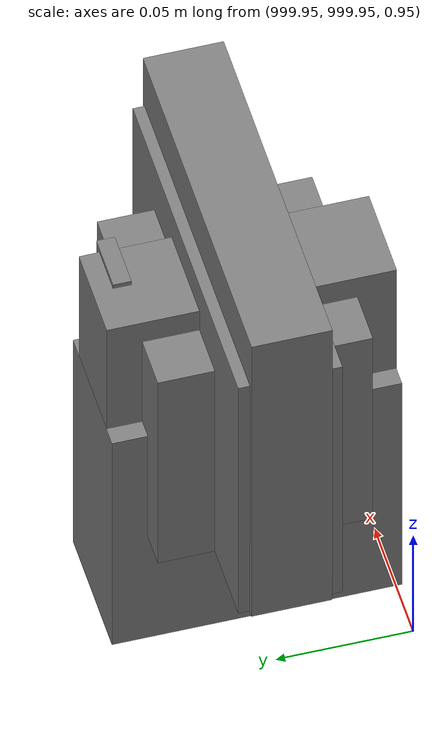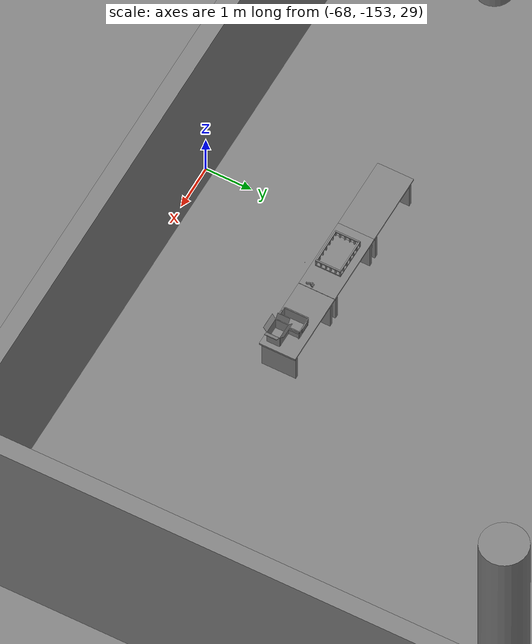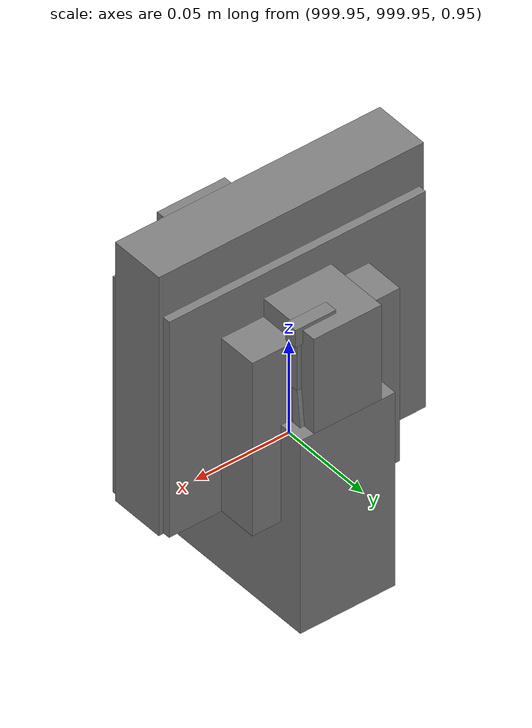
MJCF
<mujoco>
    <option gravity="0.000000000 0.000000000 -9.810000420" timestep="0.0049999999" integrator="implicitfast" density="1.225" viscosity="1.8000001e-05" noslip_iterations="10" iterations="100" sdf_iterations="50">
        <flag multiccd="disable"/>
    </option>
    <size memory="1000M"/>
    <compiler coordinate="local"/>
    <worldbody>
        <light cutoff="30" pos="0 1 1" dir="0 -1 -2"/>
        <light cutoff="30" pos="0 -1 1" dir="0 1 -2"/>
        <body pos="-64.866622925 -149.383972168 30.183746338" euler="89.999984741 89.999946594 0.000000000" name="openloong_gripper_2f85_fix_base_usda_bluebox_01">
            <geom contype="1" conaffinity="1" density="1000" type="box" material="" rgba="0.500000000 0.500000000 0.500000000 1.000000000" solimp="0.899999976 0.949999988 0.001000000" friction="1.000000000 0.005000000 0.000100000" solref="0.020000000 1.000000000" margin="0" condim="3" group="0" pos="0.276580811 0.187225342 0.000068665" quat="0.707106948 0.000077471 0.707106352 0.000077486" size="0.100000001 0.057999998 0.010000000" name="openloong_gripper_2f85_fix_base_usda_geom_8C0B86BC_B73D_4475_B321_79D40C877243"/>
            <geom contype="1" conaffinity="1" density="1000" type="box" material="" rgba="0.500000000 0.500000000 0.500000000 1.000000000" solimp="0.899999976 0.949999988 0.001000000" friction="1.000000000 0.005000000 0.000100000" solref="0.020000000 1.000000000" margin="0" condim="3" group="0" pos="0.000000000 0.002883911 0.000000000" quat="0.999999881 0.000000000 0.000000000 0.000000000" size="0.254000008 0.003000000 0.172000006" name="openloong_gripper_2f85_fix_base_usda_geom_E271C356_72C6_47DD_8921_C6BCF0F03C82"/>
            <geom contype="1" conaffinity="1" density="1000" type="box" material="" rgba="0.500000000 0.500000000 0.500000000 1.000000000" solimp="0.899999976 0.949999988 0.001000000" friction="1.000000000 0.005000000 0.000100000" solref="0.020000000 1.000000000" margin="0" condim="3" group="0" pos="0.000000000 0.124874115 0.173484802" quat="0.999796331 0.020176515 -0.000000015 0.000000030" size="0.259999990 0.119999997 0.007000000" name="openloong_gripper_2f85_fix_base_usda_geom_916EF327_0021_4CF9_B35A_8D8EDC3AB02B"/>
            <geom contype="1" conaffinity="1" density="1000" type="box" material="" rgba="0.500000000 0.500000000 0.500000000 1.000000000" solimp="0.899999976 0.949999988 0.001000000" friction="1.000000000 0.005000000 0.000100000" solref="0.020000000 1.000000000" margin="0" condim="3" group="0" pos="0.000000000 0.124874115 -0.173469543" quat="0.999796331 -0.020176545 -0.000000015 0.000000000" size="0.259999990 0.119999997 0.007000000" name="openloong_gripper_2f85_fix_base_usda_geom_96249C3C_CB50_4A34_9C9F_B1E06F8F501D"/>
            <geom contype="1" conaffinity="1" density="1000" type="box" material="" rgba="0.500000000 0.500000000 0.500000000 1.000000000" solimp="0.899999976 0.949999988 0.001000000" friction="1.000000000 0.005000000 0.000100000" solref="0.020000000 1.000000000" margin="0" condim="3" group="0" pos="0.000000000 0.214008331 0.188980103" quat="0.999912977 0.013176724 0.000000015 0.000000000" size="0.259999990 0.029999999 0.012500000" name="openloong_gripper_2f85_fix_base_usda_geom_93009352_0C33_4900_9D56_37122C33166B"/>
            <geom contype="1" conaffinity="1" density="1000" type="box" material="" rgba="0.500000000 0.500000000 0.500000000 1.000000000" solimp="0.899999976 0.949999988 0.001000000" friction="1.000000000 0.005000000 0.000100000" solref="0.020000000 1.000000000" margin="0" condim="3" group="0" pos="-0.258361816 0.125289917 0.001876831" quat="0.702796936 -0.020792112 0.710783124 0.020769298" size="0.189999998 0.119999997 0.009000000" name="openloong_gripper_2f85_fix_base_usda_geom_61EA94E2_F1C9_473A_A218_42D502D150F4"/>
            <geom contype="1" conaffinity="1" density="1000" type="box" material="" rgba="0.500000000 0.500000000 0.500000000 1.000000000" solimp="0.899999976 0.949999988 0.001000000" friction="1.000000000 0.005000000 0.000100000" solref="0.020000000 1.000000000" margin="0" condim="3" group="0" pos="0.000000000 0.214008331 -0.188980103" quat="0.999912977 -0.013176769 0.000000030 0.000000015" size="0.259999990 0.029999999 0.012500000" name="openloong_gripper_2f85_fix_base_usda_geom_893B7C8B_29AA_4D41_B2D7_2EFC9772BBC7"/>
            <geom contype="1" conaffinity="1" density="1000" type="box" material="" rgba="0.500000000 0.500000000 0.500000000 1.000000000" solimp="0.899999976 0.949999988 0.001000000" friction="1.000000000 0.005000000 0.000100000" solref="0.020000000 1.000000000" margin="0" condim="3" group="0" pos="-0.276611328 0.187225342 0.000068665" quat="0.707106650 0.000077441 0.707106709 0.000077456" size="0.100000001 0.057999998 0.010000000" name="openloong_gripper_2f85_fix_base_usda_geom_DF6257A8_CA19_4DAD_8625_D3EC43E65730"/>
            <geom contype="1" conaffinity="1" density="1000" type="box" material="" rgba="0.500000000 0.500000000 0.500000000 1.000000000" solimp="0.899999976 0.949999988 0.001000000" friction="1.000000000 0.005000000 0.000100000" solref="0.020000000 1.000000000" margin="0" condim="3" group="0" pos="0.258331299 0.125289917 0.001876831" quat="0.702851415 0.018856421 0.710823774 -0.019329369" size="0.189999998 0.119999997 0.009000000" name="openloong_gripper_2f85_fix_base_usda_geom_B6240214_15AC_49B2_A295_4A9115013BAE"/>
            <freejoint name="openloong_gripper_2f85_fix_base_usda_bluebox_01_joint"/>
            <site size="0.005000000 0.005000000 0.005000000" rgba="0.500000000 0.500000000 0.500000000 1.000000000" pos="0.000000000 0.000000000 0.000000000" quat="0.999961913 0.008726534 0.000000000 0.000000000" group="0" type="sphere" name="openloong_gripper_2f85_fix_base_usda_bluebox_01site"/>
        </body>
        <body pos="-64.496299744 -149.491867065 30.235729218" euler="0.000000000 0.000000000 89.999946594" name="openloong_gripper_2f85_fix_base_usda_cardboardbox_01">
            <geom contype="1" conaffinity="1" density="1000" type="box" material="" rgba="0.500000000 0.500000000 0.500000000 1.000000000" solimp="0.899999976 0.949999988 0.001000000" friction="1.000000000 0.005000000 0.000100000" solref="0.020000000 1.000000000" margin="0" condim="3" group="0" pos="-0.003166199 -0.004086494 0.005052090" quat="1.000000000 0.000000000 0.000000000 0.000000000" size="0.142499998 0.177500010 0.005000000" name="openloong_gripper_2f85_fix_base_usda_geom_F351C04F_93F5_4688_81AA_844E49FACB26"/>
            <geom contype="1" conaffinity="1" density="1000" type="box" material="" rgba="0.500000000 0.500000000 0.500000000 1.000000000" solimp="0.899999976 0.949999988 0.001000000" friction="1.000000000 0.005000000 0.000100000" solref="0.020000000 1.000000000" margin="0" condim="3" group="0" pos="-0.003166199 0.170316696 0.150570869" quat="1.000000000 0.000000000 0.000000000 0.000000000" size="0.142499998 0.005000000 0.149999991" name="openloong_gripper_2f85_fix_base_usda_geom_46C7F9CB_DE84_4188_B515_7438E2964803"/>
            <geom contype="1" conaffinity="1" density="1000" type="box" material="" rgba="0.500000000 0.500000000 0.500000000 1.000000000" solimp="0.899999976 0.949999988 0.001000000" friction="1.000000000 0.005000000 0.000100000" solref="0.020000000 1.000000000" margin="0" condim="3" group="0" pos="-0.147399902 -0.005307198 0.150570869" quat="1.000000000 0.000000000 0.000000000 0.000000000" size="0.005000000 0.177500010 0.149999991" name="openloong_gripper_2f85_fix_base_usda_geom_7BF87732_7A4F_4AF4_A835_C65EF02D6D3A"/>
            <geom contype="1" conaffinity="1" density="1000" type="box" material="" rgba="0.500000000 0.500000000 0.500000000 1.000000000" solimp="0.899999976 0.949999988 0.001000000" friction="1.000000000 0.005000000 0.000100000" solref="0.020000000 1.000000000" margin="0" condim="3" group="0" pos="0.140275955 -0.005307198 0.150570869" quat="1.000000000 0.000000000 0.000000000 0.000000000" size="0.005000000 0.177500010 0.149999991" name="openloong_gripper_2f85_fix_base_usda_geom_96180D70_F83B_40B0_BF33_A1C2D0E084A7"/>
            <geom contype="1" conaffinity="1" density="1000" type="box" material="" rgba="0.500000000 0.500000000 0.500000000 1.000000000" solimp="0.899999976 0.949999988 0.001000000" friction="1.000000000 0.005000000 0.000100000" solref="0.020000000 1.000000000" margin="0" condim="3" group="0" pos="-0.003166199 -0.181550980 0.150570869" quat="1.000000000 0.000000000 0.000000000 0.000000000" size="0.142499998 0.005000000 0.149999991" name="openloong_gripper_2f85_fix_base_usda_geom_768E99FB_CAD2_4930_BFA8_CB6B194FB1F6"/>
            <freejoint name="openloong_gripper_2f85_fix_base_usda_cardboardbox_01_joint"/>
            <site size="0.005000000 0.005000000 0.005000000" rgba="0.500000000 0.500000000 0.500000000 1.000000000" pos="0.000000000 0.000000000 0.000000000" quat="0.999961913 0.008726535 0.000000000 0.000000000" group="0" type="sphere" name="openloong_gripper_2f85_fix_base_usda_site_5DC07B14_765A_4204_9308_CB2275A197B4"/>
            <body pos="0.139160156 -0.004048347 0.301930904" euler="-179.999954224 49.383502960 179.999954224" name="openloong_gripper_2f85_fix_base_usda_A1_006">
                <geom contype="1" conaffinity="1" density="1000" type="box" material="" rgba="0.500000000 0.500000000 0.500000000 1.000000000" solimp="0.899999976 0.949999988 0.001000000" friction="1.000000000 0.005000000 0.000100000" solref="0.020000000 1.000000000" margin="0" condim="3" group="0" pos="-0.071587563 0.000009537 0.001745224" quat="0.999999881 0.000000000 0.000000000 0.000000000" size="0.071249999 0.179999992 0.002500000" name="openloong_gripper_2f85_fix_base_usda_geom_160D8F45_2814_4582_B54D_4376BC48A916"/>
                <joint armature="0" stiffness="0.07" damping="0.0099999998" axis="0.000000 1.000000 0.000000" type="hinge" name="openloong_gripper_2f85_fix_base_usda_A1_006"/>
            </body>
            <body pos="-0.145902634 -0.004086494 0.301938057" euler="-180.000000000 -60.000011444 -180.000000000" name="openloong_gripper_2f85_fix_base_usda_A2_006">
                <geom contype="1" conaffinity="1" density="1000" type="box" material="" rgba="0.500000000 0.500000000 0.500000000 1.000000000" solimp="0.899999976 0.949999988 0.001000000" friction="1.000000000 0.005000000 0.000100000" solref="0.020000000 1.000000000" margin="0" condim="3" group="0" pos="0.071268082 0.000009537 0.002717972" quat="0.000002921 0.000000000 -0.000000030 0.999999881" size="0.071249999 0.179999992 0.002500000" name="openloong_gripper_2f85_fix_base_usda_geom_3B5CC5F0_4122_4146_AC6E_A9772E42E882"/>
                <joint armature="0" stiffness="0.07" damping="0.0099999998" axis="0.000000 1.000000 0.000000" type="hinge" name="openloong_gripper_2f85_fix_base_usda_A2_006"/>
            </body>
            <body pos="-0.003385544 0.175991058 0.301930904" euler="-125.858116150 -0.000004561 0.000002331" name="openloong_gripper_2f85_fix_base_usda_B2_006">
                <geom contype="1" conaffinity="1" density="1000" type="box" material="" rgba="0.500000000 0.500000000 0.500000000 1.000000000" solimp="0.899999976 0.949999988 0.001000000" friction="1.000000000 0.005000000 0.000100000" solref="0.020000000 1.000000000" margin="0" condim="3" group="0" pos="0.000009537 -0.070939064 -0.002470016" quat="0.999614120 0.027776197 -0.000000015 0.000000030" size="0.137500003 0.064999998 0.005000000" name="openloong_gripper_2f85_fix_base_usda_geom_C43FD400_2056_4A8B_B35F_7292F67580EF"/>
                <joint armature="0" stiffness="0.07" damping="0.0099999998" axis="1.000000 0.000000 0.000000" type="hinge" name="openloong_gripper_2f85_fix_base_usda_B2_006"/>
            </body>
            <body pos="-0.003385544 -0.184140205 0.301938057" euler="147.805557251 0.000000000 0.000000000" name="openloong_gripper_2f85_fix_base_usda_B1_006">
                <geom contype="1" conaffinity="1" density="1000" type="box" material="" rgba="0.500000000 0.500000000 0.500000000 1.000000000" solimp="0.899999976 0.949999988 0.001000000" friction="1.000000000 0.005000000 0.000100000" solref="0.020000000 1.000000000" margin="0" condim="3" group="0" pos="-0.000028610 0.070202351 -0.002703667" quat="0.999614179 -0.027776167 0.000000000 0.000000000" size="0.137500003 0.064999998 0.005000000" name="openloong_gripper_2f85_fix_base_usda_geom_9043DB6E_1CD9_4D14_A073_442C754BE4BF"/>
                <joint armature="0" stiffness="0.07" damping="0.0099999998" axis="1.000000 0.000000 0.000000" type="hinge" name="openloong_gripper_2f85_fix_base_usda_B1_006"/>
            </body>
        </body>
        <body pos="-65.882858276 -149.481979370 30.229999542" euler="-64.487716675 0.000000000 0.000000000" name="openloong_gripper_2f85_fix_base_usda_Barcode">
            <geom contype="1" conaffinity="1" density="1000" type="box" material="" rgba="0.500000000 0.500000000 0.500000000 1.000000000" solimp="0.899999976 0.949999988 0.001000000" friction="1.000000000 0.005000000 0.000100000" solref="0.020000000 1.000000000" margin="0" condim="3" group="0" pos="0.000000000 0.013038635 0.001419067" quat="0.000000000 0.000000000 0.000000000 1.000000119" size="0.034000002 0.010000000 0.017999999" name="openloong_gripper_2f85_fix_base_usda_geom_AD6990A5_0F21_43B9_B84D_C911C206E955"/>
            <geom contype="1" conaffinity="1" density="1000" type="box" material="" rgba="0.500000000 0.500000000 0.500000000 1.000000000" solimp="0.899999976 0.949999988 0.001000000" friction="1.000000000 0.005000000 0.000100000" solref="0.020000000 1.000000000" margin="0" condim="3" group="0" pos="0.000000000 -0.035301208 -0.007095337" quat="0.000000000 0.000000000 -0.043619365 0.999048233" size="0.028999999 0.010000000 0.020000000" name="openloong_gripper_2f85_fix_base_usda_geom_9DD5A40B_4955_4CA4_ADFF_DBE829968D10"/>
            <geom contype="1" conaffinity="1" density="1000" type="box" material="" rgba="0.500000000 0.500000000 0.500000000 1.000000000" solimp="0.899999976 0.949999988 0.001000000" friction="1.000000000 0.005000000 0.000100000" solref="0.020000000 1.000000000" margin="0" condim="3" group="0" pos="0.000000000 -0.043411255 -0.011749268" quat="0.922262907 0.386563420 0.000000000 0.000000000" size="0.026000001 0.010000000 0.020000000" name="openloong_gripper_2f85_fix_base_usda_geom_33E62E0E_A8AD_4E0D_A719_7610649CD8E0"/>
            <geom contype="1" conaffinity="1" density="1000" type="box" material="" rgba="0.500000000 0.500000000 0.500000000 1.000000000" solimp="0.899999976 0.949999988 0.001000000" friction="1.000000000 0.005000000 0.000100000" solref="0.020000000 1.000000000" margin="0" condim="3" group="0" pos="0.000000000 -0.016967773 -0.031860352" quat="0.000000000 0.000000000 0.000000000 1.000000119" size="0.008000000 0.010000000 0.013000000" name="openloong_gripper_2f85_fix_base_usda_geom_D45BA9CD_EEF0_4952_A585_7998EF1F5F23"/>
            <geom contype="1" conaffinity="1" density="1000" type="box" material="" rgba="0.500000000 0.500000000 0.500000000 1.000000000" solimp="0.899999976 0.949999988 0.001000000" friction="1.000000000 0.005000000 0.000100000" solref="0.020000000 1.000000000" margin="0" condim="3" group="0" pos="0.000000000 -0.001869202 0.000312805" quat="0.953716993 0.300705761 0.000000000 0.000000000" size="0.032000002 0.010000000 0.018999999" name="openloong_gripper_2f85_fix_base_usda_geom_A0B306B6_6C2C_4E5C_921A_59F98214FC22"/>
            <geom contype="1" conaffinity="1" density="1000" type="box" material="" rgba="0.500000000 0.500000000 0.500000000 1.000000000" solimp="0.899999976 0.949999988 0.001000000" friction="1.000000000 0.005000000 0.000100000" solref="0.020000000 1.000000000" margin="0" condim="3" group="0" pos="0.000000000 -0.019531250 -0.003173828" quat="0.953716993 0.300705761 0.000000000 0.000000000" size="0.030999999 0.010000000 0.020000000" name="openloong_gripper_2f85_fix_base_usda_geom_CF44CFA6_D6E5_4310_8AD5_3AE0533BFED8"/>
            <geom contype="1" conaffinity="1" density="1000" type="box" material="" rgba="0.500000000 0.500000000 0.500000000 1.000000000" solimp="0.899999976 0.949999988 0.001000000" friction="1.000000000 0.005000000 0.000100000" solref="0.020000000 1.000000000" margin="0" condim="3" group="0" pos="0.000000000 -0.035301208 -0.007095337" quat="0.953716993 0.300705761 0.000000000 0.000000000" size="0.028999999 0.010000000 0.020000000" name="openloong_gripper_2f85_fix_base_usda_geom_34898D5F_A50B_4DA2_9B0E_BC1FDC8D052C"/>
            <geom contype="1" conaffinity="1" density="1000" type="box" material="" rgba="0.500000000 0.500000000 0.500000000 1.000000000" solimp="0.899999976 0.949999988 0.001000000" friction="1.000000000 0.005000000 0.000100000" solref="0.020000000 1.000000000" margin="0" condim="3" group="0" pos="0.000000000 -0.042617798 -0.071121216" quat="0.000000000 0.000000000 0.000000000 1.000000119" size="0.013000000 0.021000000 0.059999999" name="openloong_gripper_2f85_fix_base_usda_geom_4474F1A1_A781_4CA7_843A_998F6CDEF264"/>
            <freejoint name="openloong_gripper_2f85_fix_base_usda_Barcode_joint"/>
            <site size="0.005000000 0.005000000 0.005000000" rgba="0.500000000 0.500000000 0.500000000 1.000000000" pos="0.000000000 0.000000000 0.000000000" quat="1.000000000 0.000000000 0.000000000 0.000000000" group="0" type="sphere" name="openloong_gripper_2f85_fix_base_usda_Barcode_site"/>
        </body>
        <body pos="-66.745018005 -149.392349243 30.184000015" euler="0.000000000 0.000000000 89.999946594" name="[22330329997373]_Basket_01">
            <geom contype="1" conaffinity="1" density="1000" type="box" material="" rgba="0.500000000 0.500000000 0.500000000 1.000000000" solimp="0.899999976 0.949999988 0.001000000" friction="1.000000000 0.005000000 0.000100000" solref="0.020000000 1.000000000" margin="0" condim="3" group="0" pos="-0.052425385 0.389207840 0.089787483" quat="0.707107008 0.000000000 0.000000000 0.707106411" size="0.014249999 0.014249999 0.059999999" name="[22330329997373]_geom_FF174827_CD7D_44F9_A6EE_369312E70651"/>
            <geom contype="1" conaffinity="1" density="1000" type="box" material="" rgba="0.500000000 0.500000000 0.500000000 1.000000000" solimp="0.899999976 0.949999988 0.001000000" friction="1.000000000 0.005000000 0.000100000" solref="0.020000000 1.000000000" margin="0" condim="3" group="0" pos="0.264015198 -0.133043289 0.089787483" quat="0.707107008 0.000000000 0.000000000 0.707106411" size="0.014249999 0.014249999 0.059999999" name="[22330329997373]_geom_8BA079E3_1CA7_4291_A86E_867DD3DFA508"/>
            <geom contype="1" conaffinity="1" density="1000" type="box" material="" rgba="0.500000000 0.500000000 0.500000000 1.000000000" solimp="0.899999976 0.949999988 0.001000000" friction="1.000000000 0.005000000 0.000100000" solref="0.020000000 1.000000000" margin="0" condim="3" group="0" pos="-0.264015198 -0.265548706 0.089793205" quat="0.707107008 0.000000000 0.000000000 0.707106411" size="0.014249999 0.014249999 0.059999999" name="[22330329997373]_geom_D901D7C6_2EBA_4D9B_8148_2C57E2F139BF"/>
            <geom contype="1" conaffinity="1" density="1000" type="box" material="" rgba="0.500000000 0.500000000 0.500000000 1.000000000" solimp="0.899999976 0.949999988 0.001000000" friction="1.000000000 0.005000000 0.000100000" solref="0.020000000 1.000000000" margin="0" condim="3" group="0" pos="-0.160263062 -0.389322281 0.089793205" quat="0.707107008 0.000000000 0.000000000 0.707106411" size="0.014249999 0.014249999 0.059999999" name="[22330329997373]_geom_FF7FEC5A_CF1D_4908_84E3_BB53B17ECD30"/>
            <geom contype="1" conaffinity="1" density="1000" type="box" material="" rgba="0.500000000 0.500000000 0.500000000 1.000000000" solimp="0.899999976 0.949999988 0.001000000" friction="1.000000000 0.005000000 0.000100000" solref="0.020000000 1.000000000" margin="0" condim="3" group="0" pos="0.162265778 -0.389322281 0.089787483" quat="0.707107008 0.000000000 0.000000000 0.707106411" size="0.014249999 0.014249999 0.059999999" name="[22330329997373]_geom_0ECDC74F_E880_4D37_B89A_15BDC8DF7C3A"/>
            <geom contype="1" conaffinity="1" density="1000" type="box" material="" rgba="0.500000000 0.500000000 0.500000000 1.000000000" solimp="0.899999976 0.949999988 0.001000000" friction="1.000000000 0.005000000 0.000100000" solref="0.020000000 1.000000000" margin="0" condim="3" group="0" pos="0.264015198 0.389207840 0.089787483" quat="0.707107008 0.000000000 0.000000000 0.707106411" size="0.014249999 0.014249999 0.059999999" name="[22330329997373]_geom_FA388997_DBDF_4711_89B4_3E90A0C7BBC2"/>
            <geom contype="1" conaffinity="1" density="1000" type="box" material="" rgba="0.500000000 0.500000000 0.500000000 1.000000000" solimp="0.899999976 0.949999988 0.001000000" friction="1.000000000 0.005000000 0.000100000" solref="0.020000000 1.000000000" margin="0" condim="3" group="0" pos="-0.264015198 -0.133043289 0.089793205" quat="0.707107008 0.000000000 0.000000000 0.707106411" size="0.014249999 0.014249999 0.059999999" name="[22330329997373]_geom_AC8E064A_A534_40FA_AB66_02E2C0438094"/>
            <geom contype="1" conaffinity="1" density="1000" type="box" material="" rgba="0.500000000 0.500000000 0.500000000 1.000000000" solimp="0.899999976 0.949999988 0.001000000" friction="1.000000000 0.005000000 0.000100000" solref="0.020000000 1.000000000" margin="0" condim="3" group="0" pos="-0.264026642 0.269256592 0.089793205" quat="0.707107008 0.000000000 0.000000000 0.707106411" size="0.014249999 0.014249999 0.059999999" name="[22330329997373]_geom_4E33EFD0_BE13_4BF2_8FEA_BEC624FD8473"/>
            <geom contype="1" conaffinity="1" density="1000" type="box" material="" rgba="0.500000000 0.500000000 0.500000000 1.000000000" solimp="0.899999976 0.949999988 0.001000000" friction="1.000000000 0.005000000 0.000100000" solref="0.020000000 1.000000000" margin="0" condim="3" group="0" pos="0.054462433 0.389207840 0.089787483" quat="0.707107008 0.000000000 0.000000000 0.707106411" size="0.014249999 0.014249999 0.059999999" name="[22330329997373]_geom_908595EE_F381_4CF2_81CC_6CF254AA27AB"/>
            <geom contype="1" conaffinity="1" density="1000" type="box" material="" rgba="0.500000000 0.500000000 0.500000000 1.000000000" solimp="0.899999976 0.949999988 0.001000000" friction="1.000000000 0.005000000 0.000100000" solref="0.020000000 1.000000000" margin="0" condim="3" group="0" pos="0.054462433 -0.389322281 0.089787483" quat="0.707107008 0.000000000 0.000000000 0.707106411" size="0.014249999 0.014249999 0.059999999" name="[22330329997373]_geom_24C049FC_64FF_43AB_8A64_090A2BFF1FED"/>
            <geom contype="1" conaffinity="1" density="1000" type="box" material="" rgba="0.500000000 0.500000000 0.500000000 1.000000000" solimp="0.899999976 0.949999988 0.001000000" friction="1.000000000 0.005000000 0.000100000" solref="0.020000000 1.000000000" margin="0" condim="3" group="0" pos="0.264015198 0.269256592 0.089793205" quat="0.707107008 0.000000000 0.000000000 0.707106411" size="0.014249999 0.014249999 0.059999999" name="[22330329997373]_geom_F7F16827_50F8_43E3_BBB2_40D339086BE7"/>
            <geom contype="1" conaffinity="1" density="1000" type="box" material="" rgba="0.500000000 0.500000000 0.500000000 1.000000000" solimp="0.899999976 0.949999988 0.001000000" friction="1.000000000 0.005000000 0.000100000" solref="0.020000000 1.000000000" margin="0" condim="3" group="0" pos="0.264015198 -0.389322281 0.089787483" quat="0.707107008 0.000000000 0.000000000 0.707106411" size="0.014249999 0.014249999 0.059999999" name="[22330329997373]_geom_9C3B0D3C_9A3C_4FBB_A70A_0F2854B231CF"/>
            <geom contype="1" conaffinity="1" density="1000" type="box" material="" rgba="0.500000000 0.500000000 0.500000000 1.000000000" solimp="0.899999976 0.949999988 0.001000000" friction="1.000000000 0.005000000 0.000100000" solref="0.020000000 1.000000000" margin="0" condim="3" group="0" pos="0.000000000 0.000000000 0.015998840" quat="0.707107008 0.000000000 0.000000000 0.707106411" size="0.403499991 0.279000014 0.015750000" name="[22330329997373]_geom_D8A5D9FE_1C88_4B94_BB7B_BDECE458B411"/>
            <geom contype="1" conaffinity="1" density="1000" type="box" material="" rgba="0.500000000 0.500000000 0.500000000 1.000000000" solimp="0.899999976 0.949999988 0.001000000" friction="1.000000000 0.005000000 0.000100000" solref="0.020000000 1.000000000" margin="0" condim="3" group="0" pos="0.000000000 -0.389476776 0.163619041" quat="0.707107008 0.000000000 0.000000000 0.707106411" size="0.015000000 0.277500004 0.015750000" name="[22330329997373]_geom_8451BF72_CCF5_4CF6_BA5A_D776DD7E08A6"/>
            <geom contype="1" conaffinity="1" density="1000" type="box" material="" rgba="0.500000000 0.500000000 0.500000000 1.000000000" solimp="0.899999976 0.949999988 0.001000000" friction="1.000000000 0.005000000 0.000100000" solref="0.020000000 1.000000000" margin="0" condim="3" group="0" pos="0.162265778 0.389207840 0.089787483" quat="0.707107008 0.000000000 0.000000000 0.707106411" size="0.014249999 0.014249999 0.059999999" name="[22330329997373]_geom_A09513D5_FC88_4DCB_8A30_5F0B0DCF84A2"/>
            <geom contype="1" conaffinity="1" density="1000" type="box" material="" rgba="0.500000000 0.500000000 0.500000000 1.000000000" solimp="0.899999976 0.949999988 0.001000000" friction="1.000000000 0.005000000 0.000100000" solref="0.020000000 1.000000000" margin="0" condim="3" group="0" pos="0.000000000 0.389471054 0.163619041" quat="0.707107008 0.000000000 0.000000000 0.707106411" size="0.015000000 0.277500004 0.015750000" name="[22330329997373]_geom_BA6B8305_9B67_4B58_959B_F48EAF7697A3"/>
            <geom contype="1" conaffinity="1" density="1000" type="box" material="" rgba="0.500000000 0.500000000 0.500000000 1.000000000" solimp="0.899999976 0.949999988 0.001000000" friction="1.000000000 0.005000000 0.000100000" solref="0.020000000 1.000000000" margin="0" condim="3" group="0" pos="-0.263511658 0.000000000 0.163619041" quat="0.707107008 0.000000000 0.000000000 0.707106411" size="0.403499991 0.015000000 0.015750000" name="[22330329997373]_geom_1E168B6F_75AE_47A3_8600_3F6083186BF9"/>
            <geom contype="1" conaffinity="1" density="1000" type="box" material="" rgba="0.500000000 0.500000000 0.500000000 1.000000000" solimp="0.899999976 0.949999988 0.001000000" friction="1.000000000 0.005000000 0.000100000" solref="0.020000000 1.000000000" margin="0" condim="3" group="0" pos="-0.264015198 0.141334534 0.089793205" quat="0.707107008 0.000000000 0.000000000 0.707106411" size="0.014249999 0.014249999 0.059999999" name="[22330329997373]_geom_E7EF0929_BB31_49D1_A5B0_038E92222BD4"/>
            <geom contype="1" conaffinity="1" density="1000" type="box" material="" rgba="0.500000000 0.500000000 0.500000000 1.000000000" solimp="0.899999976 0.949999988 0.001000000" friction="1.000000000 0.005000000 0.000100000" solref="0.020000000 1.000000000" margin="0" condim="3" group="0" pos="0.264015198 -0.265548706 0.089787483" quat="0.707107008 0.000000000 0.000000000 0.707106411" size="0.014249999 0.014249999 0.059999999" name="[22330329997373]_geom_AB970C63_590A_41BB_AADF_BFCF9DC4E39C"/>
            <geom contype="1" conaffinity="1" density="1000" type="box" material="" rgba="0.500000000 0.500000000 0.500000000 1.000000000" solimp="0.899999976 0.949999988 0.001000000" friction="1.000000000 0.005000000 0.000100000" solref="0.020000000 1.000000000" margin="0" condim="3" group="0" pos="-0.160263062 0.389207840 0.089787483" quat="0.707107008 0.000000000 0.000000000 0.707106411" size="0.014249999 0.014249999 0.059999999" name="[22330329997373]_geom_09697125_87A5_4157_BC52_37E7AC7D135D"/>
            <geom contype="1" conaffinity="1" density="1000" type="box" material="" rgba="0.500000000 0.500000000 0.500000000 1.000000000" solimp="0.899999976 0.949999988 0.001000000" friction="1.000000000 0.005000000 0.000100000" solref="0.020000000 1.000000000" margin="0" condim="3" group="0" pos="-0.052425385 -0.389322281 0.089787483" quat="0.707107008 0.000000000 0.000000000 0.707106411" size="0.014249999 0.014249999 0.059999999" name="[22330329997373]_geom_C3424C5F_3720_44C9_918F_ACF6F21D3924"/>
            <geom contype="1" conaffinity="1" density="1000" type="box" material="" rgba="0.500000000 0.500000000 0.500000000 1.000000000" solimp="0.899999976 0.949999988 0.001000000" friction="1.000000000 0.005000000 0.000100000" solref="0.020000000 1.000000000" margin="0" condim="3" group="0" pos="-0.264026642 -0.389322281 0.089793205" quat="0.707107008 0.000000000 0.000000000 0.707106411" size="0.014249999 0.014249999 0.059999999" name="[22330329997373]_geom_1FFD2D51_7DB7_4CF3_8B8C_BE600630C570"/>
            <geom contype="1" conaffinity="1" density="1000" type="box" material="" rgba="0.500000000 0.500000000 0.500000000 1.000000000" solimp="0.899999976 0.949999988 0.001000000" friction="1.000000000 0.005000000 0.000100000" solref="0.020000000 1.000000000" margin="0" condim="3" group="0" pos="0.264015198 0.141334534 0.089787483" quat="0.707107008 0.000000000 0.000000000 0.707106411" size="0.014249999 0.014249999 0.059999999" name="[22330329997373]_geom_851CA8AF_1E8E_440C_8584_AE51674004A4"/>
            <geom contype="1" conaffinity="1" density="1000" type="box" material="" rgba="0.500000000 0.500000000 0.500000000 1.000000000" solimp="0.899999976 0.949999988 0.001000000" friction="1.000000000 0.005000000 0.000100000" solref="0.020000000 1.000000000" margin="0" condim="3" group="0" pos="-0.264015198 0.389207840 0.089793205" quat="0.707107008 0.000000000 0.000000000 0.707106411" size="0.014249999 0.014249999 0.059999999" name="[22330329997373]_geom_7287CD77_F274_4868_8A7A_8C7619D46218"/>
            <geom contype="1" conaffinity="1" density="1000" type="box" material="" rgba="0.500000000 0.500000000 0.500000000 1.000000000" solimp="0.899999976 0.949999988 0.001000000" friction="1.000000000 0.005000000 0.000100000" solref="0.020000000 1.000000000" margin="0" condim="3" group="0" pos="0.264015198 0.004480362 0.089787483" quat="0.707107008 0.000000000 0.000000000 0.707106411" size="0.014249999 0.014249999 0.059999999" name="[22330329997373]_geom_51EE14AC_554B_4785_8768_428E08FDEABB"/>
            <geom contype="1" conaffinity="1" density="1000" type="box" material="" rgba="0.500000000 0.500000000 0.500000000 1.000000000" solimp="0.899999976 0.949999988 0.001000000" friction="1.000000000 0.005000000 0.000100000" solref="0.020000000 1.000000000" margin="0" condim="3" group="0" pos="0.263694763 -0.000011444 0.163619041" quat="0.707107008 0.000000000 0.000000000 0.707106411" size="0.403499991 0.015000000 0.015750000" name="[22330329997373]_geom_20A448AE_690E_48F5_902E_DCEB8584E25C"/>
            <geom contype="1" conaffinity="1" density="1000" type="box" material="" rgba="0.500000000 0.500000000 0.500000000 1.000000000" solimp="0.899999976 0.949999988 0.001000000" friction="1.000000000 0.005000000 0.000100000" solref="0.020000000 1.000000000" margin="0" condim="3" group="0" pos="-0.264015198 0.004480362 0.089793205" quat="0.707107008 0.000000000 0.000000000 0.707106411" size="0.014249999 0.014249999 0.059999999" name="[22330329997373]_geom_402991A4_D994_45DD_B1ED_2CC805F9C40D"/>
            <freejoint name="[22330329997373]_joint_54380785_99AA_4CE6_9044_D28CB6A63A1B"/>
        </body>
        <body pos="0.000000000 0.000000000 0.000000000" euler="0.000000000 0.000000000 0.000000000" name="Static Objects_Static Objects">
            <geom contype="1" conaffinity="1" density="1000" type="box" material="" rgba="0.500000000 0.500000000 0.500000000 1.000000000" solimp="0.899999976 0.949999988 0.001000000" friction="1.000000000 0.005000000 0.000100000" solref="0.020000000 1.000000000" margin="0" condim="3" group="0" pos="-67.544113159 -149.365814209 29.727830887" quat="0.500000417 0.499999970 0.499999553 0.499999970" size="0.381000012 0.319999993 0.041000001" name="Static Objects_geom_15E54451_C476_44AF_92BB_61D0DBAD12C5"/>
            <geom contype="1" conaffinity="1" density="1000" type="box" material="" rgba="0.500000000 0.500000000 0.500000000 1.000000000" solimp="0.899999976 0.949999988 0.001000000" friction="1.000000000 0.005000000 0.000100000" solref="0.020000000 1.000000000" margin="0" condim="3" group="0" pos="-68.239501953 -149.365814209 30.086868286" quat="0.500000417 0.499999970 0.499999553 0.499999970" size="0.370999992 0.039500002 0.745000005" name="Static Objects_geom_48E396F3_F078_4786_9061_A87FBB481F7D"/>
            <geom contype="1" conaffinity="1" density="1000" type="box" material="" rgba="0.500000000 0.500000000 0.500000000 1.000000000" solimp="0.899999976 0.949999988 0.001000000" friction="1.000000000 0.005000000 0.000100000" solref="0.020000000 1.000000000" margin="0" condim="3" group="0" pos="-68.239501953 -149.365814209 30.147235870" quat="0.500000417 0.499999970 0.499999553 0.499999970" size="0.400000006 0.022000000 0.800000012" name="Static Objects_geom_3B249740_C1AE_4593_BDD9_F76753755CDF"/>
            <geom contype="1" conaffinity="1" density="1000" type="box" material="" rgba="0.500000000 0.500000000 0.500000000 1.000000000" solimp="0.899999976 0.949999988 0.001000000" friction="1.000000000 0.005000000 0.000100000" solref="0.020000000 1.000000000" margin="0" condim="3" group="0" pos="-68.934890747 -149.365814209 29.727830887" quat="0.500000417 0.499999970 0.499999553 0.499999970" size="0.381000012 0.319999993 0.041000001" name="Static Objects_geom_D0320059_CE43_47BD_B7FE_873FD069018C"/>
            <geom contype="1" conaffinity="1" density="1000" type="box" material="" rgba="0.500000000 0.500000000 0.500000000 1.000000000" solimp="0.899999976 0.949999988 0.001000000" friction="1.000000000 0.005000000 0.000100000" solref="0.020000000 1.000000000" margin="0" condim="3" group="0" pos="-68.239501953 -149.365814209 29.561563492" quat="0.500000417 0.499999970 0.499999553 0.499999970" size="0.020000000 0.022000000 0.660000026" name="Static Objects_geom_B3C23A49_6913_4FAC_A951_CA1CE36794A8"/>
            <geom contype="1" conaffinity="1" density="1000" type="box" material="" rgba="0.500000000 0.500000000 0.500000000 1.000000000" solimp="0.899999976 0.949999988 0.001000000" friction="1.000000000 0.005000000 0.000100000" solref="0.020000000 1.000000000" margin="0" condim="3" group="0" pos="-65.945671082 -149.365814209 29.727830887" quat="0.500000417 0.499999970 0.499999553 0.499999970" size="0.381000012 0.319999993 0.041000001" name="Static Objects_geom_17B0DA80_1140_4E9C_B6E6_04FE70B5DA59"/>
            <geom contype="1" conaffinity="1" density="1000" type="box" material="" rgba="0.500000000 0.500000000 0.500000000 1.000000000" solimp="0.899999976 0.949999988 0.001000000" friction="1.000000000 0.005000000 0.000100000" solref="0.020000000 1.000000000" margin="0" condim="3" group="0" pos="-66.641059875 -149.365814209 30.086868286" quat="0.500000417 0.499999970 0.499999553 0.499999970" size="0.370999992 0.039500002 0.745000005" name="Static Objects_geom_4A73AB9E_DB5E_4D3C_9EE9_EB654ED17C37"/>
            <geom contype="1" conaffinity="1" density="1000" type="box" material="" rgba="0.500000000 0.500000000 0.500000000 1.000000000" solimp="0.899999976 0.949999988 0.001000000" friction="1.000000000 0.005000000 0.000100000" solref="0.020000000 1.000000000" margin="0" condim="3" group="0" pos="-66.641059875 -149.365814209 30.147235870" quat="0.500000417 0.499999970 0.499999553 0.499999970" size="0.400000006 0.022000000 0.800000012" name="Static Objects_geom_3EF1C458_1425_4EDE_993B_188F9F1F87D9"/>
            <geom contype="1" conaffinity="1" density="1000" type="box" material="" rgba="0.500000000 0.500000000 0.500000000 1.000000000" solimp="0.899999976 0.949999988 0.001000000" friction="1.000000000 0.005000000 0.000100000" solref="0.020000000 1.000000000" margin="0" condim="3" group="0" pos="-67.336448669 -149.365814209 29.727830887" quat="0.500000417 0.499999970 0.499999553 0.499999970" size="0.381000012 0.319999993 0.041000001" name="Static Objects_geom_0E7DD320_3261_4A1C_97C8_477F045EB939"/>
            <geom contype="1" conaffinity="1" density="1000" type="box" material="" rgba="0.500000000 0.500000000 0.500000000 1.000000000" solimp="0.899999976 0.949999988 0.001000000" friction="1.000000000 0.005000000 0.000100000" solref="0.020000000 1.000000000" margin="0" condim="3" group="0" pos="-66.641059875 -149.365814209 29.561563492" quat="0.500000417 0.499999970 0.499999553 0.499999970" size="0.020000000 0.022000000 0.660000026" name="Static Objects_geom_6DE7DB26_EAA1_4D1C_9E12_3DDE81264CB1"/>
            <geom contype="1" conaffinity="1" density="1000" type="box" material="" rgba="0.500000000 0.500000000 0.500000000 1.000000000" solimp="0.899999976 0.949999988 0.001000000" friction="1.000000000 0.005000000 0.000100000" solref="0.020000000 1.000000000" margin="0" condim="3" group="0" pos="-64.338577271 -149.365814209 29.727830887" quat="0.500000417 0.499999970 0.499999553 0.499999970" size="0.381000012 0.319999993 0.041000001" name="Static Objects_geom_A18A182C_C3B1_4C53_ACFB_7E25DD5495F5"/>
            <geom contype="1" conaffinity="1" density="1000" type="box" material="" rgba="0.500000000 0.500000000 0.500000000 1.000000000" solimp="0.899999976 0.949999988 0.001000000" friction="1.000000000 0.005000000 0.000100000" solref="0.020000000 1.000000000" margin="0" condim="3" group="0" pos="-65.033966064 -149.365814209 30.086868286" quat="0.500000417 0.499999970 0.499999553 0.499999970" size="0.370999992 0.039500002 0.745000005" name="Static Objects_geom_72A30D9B_F86A_473A_9B6F_8FE7161B6B33"/>
            <geom contype="1" conaffinity="1" density="1000" type="box" material="" rgba="0.500000000 0.500000000 0.500000000 1.000000000" solimp="0.899999976 0.949999988 0.001000000" friction="1.000000000 0.005000000 0.000100000" solref="0.020000000 1.000000000" margin="0" condim="3" group="0" pos="-65.033966064 -149.365814209 30.147235870" quat="0.500000417 0.499999970 0.499999553 0.499999970" size="0.400000006 0.022000000 0.800000012" name="Static Objects_geom_C4A1C98E_87B3_4ACA_B0AE_BF16573B2946"/>
            <geom contype="1" conaffinity="1" density="1000" type="box" material="" rgba="0.500000000 0.500000000 0.500000000 1.000000000" solimp="0.899999976 0.949999988 0.001000000" friction="1.000000000 0.005000000 0.000100000" solref="0.020000000 1.000000000" margin="0" condim="3" group="0" pos="-65.729354858 -149.365814209 29.727830887" quat="0.500000417 0.499999970 0.499999553 0.499999970" size="0.381000012 0.319999993 0.041000001" name="Static Objects_geom_7C9E9718_F1D1_480B_988D_0F6E7452F2B9"/>
            <geom contype="1" conaffinity="1" density="1000" type="box" material="" rgba="0.500000000 0.500000000 0.500000000 1.000000000" solimp="0.899999976 0.949999988 0.001000000" friction="1.000000000 0.005000000 0.000100000" solref="0.020000000 1.000000000" margin="0" condim="3" group="0" pos="-65.033966064 -149.365814209 29.561563492" quat="0.500000417 0.499999970 0.499999553 0.499999970" size="0.020000000 0.022000000 0.660000026" name="Static Objects_geom_41F8AD3A_7737_4F36_835A_235906E38BC1"/>
            <geom contype="1" conaffinity="1" density="1000" type="box" material="" rgba="0.500000000 0.500000000 0.500000000 1.000000000" solimp="0.899999976 0.949999988 0.001000000" friction="1.000000000 0.005000000 0.000100000" solref="0.020000000 1.000000000" margin="0" condim="3" group="0" pos="-61.754566193 -137.853729248 33.906845093" quat="0.707107067 0.000000000 0.000000000 0.707106471" size="0.759999990 0.759999990 4.500000000" name="Static Objects_geom_1414568B_4AD5_4F52_854E_BCB3C2D7D55D"/>
            <geom contype="1" conaffinity="1" density="1000" type="box" material="" rgba="0.500000000 0.500000000 0.500000000 1.000000000" solimp="0.899999976 0.949999988 0.001000000" friction="1.000000000 0.005000000 0.000100000" solref="0.020000000 1.000000000" margin="0" condim="3" group="0" pos="-57.511135101 -144.927108765 31.707921982" quat="1.000000000 0.000000000 0.000000000 0.000000000" size="0.200000003 8.000000000 2.299999952" name="Static Objects_geom_3019033F_D29B_441F_AEC9_9E1179188A27"/>
            <geom contype="1" conaffinity="1" density="1000" type="box" material="" rgba="0.500000000 0.500000000 0.500000000 1.000000000" solimp="0.899999976 0.949999988 0.001000000" friction="1.000000000 0.005000000 0.000100000" solref="0.020000000 1.000000000" margin="0" condim="3" group="0" pos="-80.517646790 -157.574050903 31.688196182" quat="0.707107067 0.000000000 0.000000000 0.707106471" size="0.600000024 0.600000024 2.299999952" name="Static Objects_geom_31C76B7A_7089_4F70_B756_131E21A73E66"/>
            <geom contype="1" conaffinity="1" density="1000" type="box" material="" rgba="0.500000000 0.500000000 0.500000000 1.000000000" solimp="0.899999976 0.949999988 0.001000000" friction="1.000000000 0.005000000 0.000100000" solref="0.020000000 1.000000000" margin="0" condim="3" group="0" pos="-80.711044312 -147.414932251 31.666158676" quat="1.000000000 0.000000000 0.000000000 0.000000000" size="0.200000003 10.000000000 2.299999952" name="Static Objects_geom_93D096F4_3EFA_4156_9FBF_FD89E0DAE42F"/>
            <geom contype="1" conaffinity="1" density="1000" type="box" material="" rgba="0.500000000 0.500000000 0.500000000 1.000000000" solimp="0.899999976 0.949999988 0.001000000" friction="1.000000000 0.005000000 0.000100000" solref="0.020000000 1.000000000" margin="0" condim="3" group="0" pos="-57.687217712 -137.434692383 31.688196182" quat="0.707107067 0.000000000 0.000000000 0.707106471" size="0.600000024 0.600000024 2.299999952" name="Static Objects_geom_5CFEED2F_E90F_44A2_863E_A84261F8F676"/>
            <geom contype="1" conaffinity="1" density="1000" type="box" material="" rgba="0.500000000 0.500000000 0.500000000 1.000000000" solimp="0.899999976 0.949999988 0.001000000" friction="1.000000000 0.005000000 0.000100000" solref="0.020000000 1.000000000" margin="0" condim="3" group="0" pos="-69.537033081 -140.263229370 31.714921951" quat="0.707107067 0.000000000 0.000000000 0.707106471" size="0.759999990 4.500000000 2.299999952" name="Static Objects_geom_9DC6F35C_ED2B_4C94_B5D7_0A5B482E91A1"/>
            <geom contype="1" conaffinity="1" density="1000" type="box" material="" rgba="0.500000000 0.500000000 0.500000000 1.000000000" solimp="0.899999976 0.949999988 0.001000000" friction="1.000000000 0.005000000 0.000100000" solref="0.020000000 1.000000000" margin="0" condim="3" group="0" pos="-80.073638916 -137.853713989 33.906845093" quat="0.707107067 0.000000000 0.000000000 0.707106471" size="0.759999990 0.759999990 4.500000000" name="Static Objects_geom_FEA312AC_75B5_4945_90A2_FEFBB9A2E2A5"/>
            <geom contype="1" conaffinity="1" density="1000" type="box" material="" rgba="0.500000000 0.500000000 0.500000000 1.000000000" solimp="0.899999976 0.949999988 0.001000000" friction="1.000000000 0.005000000 0.000100000" solref="0.020000000 1.000000000" margin="0" condim="3" group="0" pos="-73.406707764 -155.734664917 31.707921982" quat="1.000000000 0.000000000 0.000000000 0.000000000" size="0.200000003 3.000000000 2.299999952" name="Static Objects_geom_177E6A19_4F35_465E_8F8C_4016E83C4E00"/>
            <geom contype="1" conaffinity="1" density="1000" type="box" material="" rgba="0.500000000 0.500000000 0.500000000 1.000000000" solimp="0.899999976 0.949999988 0.001000000" friction="1.000000000 0.005000000 0.000100000" solref="0.020000000 1.000000000" margin="0" condim="3" group="0" pos="-68.497543335 -137.448257446 31.707921982" quat="0.707107067 0.000000000 0.000000000 0.707106471" size="0.200000003 14.000000000 2.299999952" name="Static Objects_geom_FF52FEAF_0EA9_44B3_A916_7E4DBBBDA70A"/>
            <geom contype="1" conaffinity="1" density="1000" type="cylinder" material="" rgba="0.500000000 0.500000000 0.500000000 1.000000000" solimp="0.899999976 0.949999988 0.001000000" friction="1.000000000 0.005000000 0.000100000" solref="0.020000000 1.000000000" margin="0" condim="3" group="0" pos="-68.868522644 -142.134506226 31.711090088" quat="0.707107067 0.000000000 0.000000000 0.707106471" size="0.509999990 2.299999952 1.000000000" name="Static Objects_geom_FA6F8981_10B6_4EF5_81CC_397AA8777C16"/>
            <geom contype="1" conaffinity="1" density="1000" type="plane" material="" rgba="0.500000000 0.500000000 0.500000000 1.000000000" solimp="0.899999976 0.949999988 0.001000000" friction="1.000000000 0.005000000 0.000100000" solref="0.020000000 1.000000000" margin="0" condim="3" group="0" pos="-72.873703003 -147.131927490 29.409669876" quat="1.000000000 0.000000000 0.000000000 0.000000000" size="18.000000000 14.000000000 1.000000000" name="Static Objects_geom_C4722D3D_32F5_4DC1_8E06_4F7086D6CFB8"/>
            <geom contype="1" conaffinity="1" density="1000" type="box" material="" rgba="0.500000000 0.500000000 0.500000000 1.000000000" solimp="0.899999976 0.949999988 0.001000000" friction="1.000000000 0.005000000 0.000100000" solref="0.020000000 1.000000000" margin="0" condim="3" group="0" pos="-79.943580627 -157.782272339 31.707921982" quat="0.707107067 0.000000000 0.000000000 0.707106471" size="0.200000003 7.000000000 2.299999952" name="Static Objects_geom_D3279475_9570_4A53_9251_BC097F783E08"/>
            <geom contype="1" conaffinity="1" density="1000" type="box" material="" rgba="0.500000000 0.500000000 0.500000000 1.000000000" solimp="0.899999976 0.949999988 0.001000000" friction="1.000000000 0.005000000 0.000100000" solref="0.020000000 1.000000000" margin="0" condim="3" group="0" pos="-65.421028137 -152.903442383 31.707921982" quat="0.707107067 0.000000000 0.000000000 0.707106471" size="0.200000003 7.800000191 2.299999952" name="Static Objects_geom_169D35C7_2B9D_4190_99B2_9EA0BFE5E579"/>
            <geom contype="1" conaffinity="1" density="1000" type="box" material="" rgba="0.500000000 0.500000000 0.500000000 1.000000000" solimp="0.899999976 0.949999988 0.001000000" friction="1.000000000 0.005000000 0.000100000" solref="0.020000000 1.000000000" margin="0" condim="3" group="0" pos="-74.776908875 -149.964416504 31.688196182" quat="1.000000000 0.000000000 0.000000000 0.000000000" size="0.600000024 0.409999996 2.299999952" name="Static Objects_geom_324FDA9D_2219_4CB9_B08F_E0707489DB63"/>
            <geom contype="1" conaffinity="1" density="1000" type="cylinder" material="" rgba="0.500000000 0.500000000 0.500000000 1.000000000" solimp="0.899999976 0.949999988 0.001000000" friction="1.000000000 0.005000000 0.000100000" solref="0.020000000 1.000000000" margin="0" condim="3" group="0" pos="-60.161884308 -142.134506226 31.711090088" quat="0.707107067 0.000000000 0.000000000 0.707106471" size="0.509999990 2.299999952 1.000000000" name="Static Objects_geom_ECD88748_30B6_455B_9307_D74E791AF92F"/>
            <geom contype="1" conaffinity="1" density="1000" type="cylinder" material="" rgba="0.500000000 0.500000000 0.500000000 1.000000000" solimp="0.899999976 0.949999988 0.001000000" friction="1.000000000 0.005000000 0.000100000" solref="0.020000000 1.000000000" margin="0" condim="3" group="0" pos="-75.382453918 -149.963455200 31.711090088" quat="0.707107067 0.000000000 0.000000000 0.707106471" size="0.409999996 2.299999952 1.000000000" name="Static Objects_geom_2C15714A_E981_41B6_85CF_C88E104C2CF8"/>
            <geom contype="1" conaffinity="1" density="1000" type="cylinder" material="" rgba="0.500000000 0.500000000 0.500000000 1.000000000" solimp="0.899999976 0.949999988 0.001000000" friction="1.000000000 0.005000000 0.000100000" solref="0.020000000 1.000000000" margin="0" condim="3" group="0" pos="-74.154960632 -149.963455200 31.711090088" quat="0.707107067 0.000000000 0.000000000 0.707106471" size="0.409999996 2.299999952 1.000000000" name="Static Objects_geom_3F180D6D_3DCF_4BD1_AAF4_3BB40344F2AF"/>
            <geom contype="1" conaffinity="1" density="1000" type="cylinder" material="" rgba="0.500000000 0.500000000 0.500000000 1.000000000" solimp="0.899999976 0.949999988 0.001000000" friction="1.000000000 0.005000000 0.000100000" solref="0.020000000 1.000000000" margin="0" condim="3" group="0" pos="-77.566612244 -142.134506226 31.711090088" quat="0.707107067 0.000000000 0.000000000 0.707106471" size="0.509999990 2.299999952 1.000000000" name="Static Objects_geom_1FF8A728_CC0B_415F_B109_4BA557EB17CD"/>
        </body>
        <body pos="-66.185310364 -149.460144043 31.166034698" euler="-86.120834351 48.718090057 -44.103862762" mocap="true" name="spotlight6_SpotLight"/>
        <body pos="1000.000000000 1000.000000000 1.000000000" euler="0.000000000 0.000000000 180.000000000" name="openloong_gripper_2f85_fix_base_usda_battery_01">
            <geom contype="1" conaffinity="1" density="1000" type="box" material="" rgba="0.500000000 0.500000000 0.500000000 1.000000000" solimp="0.899999976 0.949999988 0.001000000" friction="1.000000000 0.005000000 0.000100000" solref="0.020000000 1.000000000" margin="0" condim="3" group="0" pos="-0.011123657 -0.041940309 0.101691343" quat="1.000000000 0.000000000 0.000000000 0.000000000" size="0.010800000 0.003375000 0.004725000" name="openloong_gripper_2f85_fix_base_usda_geom_ABF1CAC8_6285_41F4_9879_EC970897A30A"/>
            <geom contype="1" conaffinity="1" density="1000" type="box" material="" rgba="0.500000000 0.500000000 0.500000000 1.000000000" solimp="0.899999976 0.949999988 0.001000000" friction="1.000000000 0.005000000 0.000100000" solref="0.020000000 1.000000000" margin="0" condim="3" group="0" pos="-0.010876465 -0.044247437 0.047066893" quat="0.998702705 -0.050920475 0.000000000 0.000000000" size="0.009450001 0.002700000 0.024975000" name="openloong_gripper_2f85_fix_base_usda_geom_076EF3B1_67CD_4D49_95A1_43C319C80B1B"/>
            <geom contype="1" conaffinity="1" density="1000" type="box" material="" rgba="0.500000000 0.500000000 0.500000000 1.000000000" solimp="0.899999976 0.949999988 0.001000000" friction="1.000000000 0.005000000 0.000100000" solref="0.020000000 1.000000000" margin="0" condim="3" group="0" pos="-0.001235962 -0.000659180 0.047381196" quat="1.000000000 0.000000000 0.000000000 0.000000000" size="0.039420001 0.039150000 0.047250003" name="openloong_gripper_2f85_fix_base_usda_geom_7C4ED431_0EC1_41ED_8006_24583287EAC2"/>
            <geom contype="1" conaffinity="1" density="1000" type="box" material="" rgba="0.500000000 0.500000000 0.500000000 1.000000000" solimp="0.899999976 0.949999988 0.001000000" friction="1.000000000 0.005000000 0.000100000" solref="0.020000000 1.000000000" margin="0" condim="3" group="0" pos="-0.010876465 -0.039138794 0.009851727" quat="1.000000000 0.000000000 0.000000000 0.000000000" size="0.009450001 0.010800000 0.013500000" name="openloong_gripper_2f85_fix_base_usda_geom_8C2237B5_047E_47F6_AD1E_78715B755297"/>
            <geom contype="1" conaffinity="1" density="1000" type="box" material="" rgba="0.500000000 0.500000000 0.500000000 1.000000000" solimp="0.899999976 0.949999988 0.001000000" friction="1.000000000 0.005000000 0.000100000" solref="0.020000000 1.000000000" margin="0" condim="3" group="0" pos="-0.010876465 -0.041528322 0.071508206" quat="1.000000000 0.000000000 0.000000000 0.000000000" size="0.009450001 0.002700000 0.027000001" name="openloong_gripper_2f85_fix_base_usda_geom_ED0FA20B_377B_47FD_A22F_60E037BF0F36"/>
            <freejoint name="openloong_gripper_2f85_fix_base_usda_battery_01_joint"/>
            <site size="0.005000000 0.005000000 0.005000000" rgba="0.500000000 0.500000000 0.500000000 1.000000000" pos="0.000000000 0.000000000 0.000000000" quat="0.999961913 0.008726500 0.000000000 0.000000000" group="0" type="sphere" name="openloong_gripper_2f85_fix_base_usda_battery_01site"/>
        </body>
        <body pos="1000.000000000 999.999938965 1.000000000" euler="0.000000000 0.000000000 180.000000000" name="openloong_gripper_2f85_fix_base_usda_intelcore_i5">
            <geom contype="1" conaffinity="1" density="1000" type="box" material="" rgba="0.500000000 0.500000000 0.500000000 1.000000000" solimp="0.899999976 0.949999988 0.001000000" friction="1.000000000 0.005000000 0.000100000" solref="0.020000000 1.000000000" margin="0" condim="3" group="0" pos="0.000000000 0.000000000 0.051722717" quat="0.707106709 0.000000000 0.000000000 -0.707106769" size="0.052800000 0.018080002 0.052800000" name="openloong_gripper_2f85_fix_base_usda_geom_00F5782E_CE8A_4B7E_B5F0_DB62E4B6AC04"/>
            <freejoint name="openloong_gripper_2f85_fix_base_usda_intelcore_i5_joint"/>
            <site size="0.005000000 0.005000000 0.005000000" rgba="0.500000000 0.500000000 0.500000000 1.000000000" pos="0.000000000 0.000000000 0.000000000" quat="0.999961913 0.008726534 0.000000000 0.000000000" group="0" type="sphere" name="openloong_gripper_2f85_fix_base_usda_intelcore_i5site"/>
        </body>
        <body pos="1000.000000000 1000.000000000 1.000000000" euler="0.000000000 0.000000000 180.000000000" name="openloong_gripper_2f85_fix_base_usda_cpu_fan">
            <geom contype="1" conaffinity="1" density="1000" type="box" material="" rgba="0.500000000 0.500000000 0.500000000 1.000000000" solimp="0.899999976 0.949999988 0.001000000" friction="1.000000000 0.005000000 0.000100000" solref="0.020000000 1.000000000" margin="0" condim="3" group="0" pos="0.000000000 0.000000000 0.070034981" quat="0.000000000 0.000000000 0.000000000 1.000000000" size="0.070700005 0.014699999 0.070700005" name="openloong_gripper_2f85_fix_base_usda_geom_524E94CE_6C96_4901_803C_5321BF161E9E"/>
            <freejoint name="openloong_gripper_2f85_fix_base_usda_cpu_fan_joint"/>
            <site size="0.005000000 0.005000000 0.005000000" rgba="0.500000000 0.500000000 0.500000000 1.000000000" pos="0.000000000 0.000000000 0.000000000" quat="0.999961913 0.008726535 0.000000000 0.000000000" group="0" type="sphere" name="openloong_gripper_2f85_fix_base_usda_cpu_fancsite"/>
        </body>
        <body pos="-66.069778442 -149.402648926 31.168775558" euler="162.434173584 85.047698975 -20.580018997" mocap="true" name="spotlight5_SpotLight"/>
        <body pos="1000.000000000 1000.000000000 1.000000000" euler="0.000011953 0.000005123 -179.999984741" name="openloong_gripper_2f85_fix_base_usda_intel_box">
            <geom contype="1" conaffinity="1" density="1000" type="box" material="" rgba="0.500000000 0.500000000 0.500000000 1.000000000" solimp="0.899999976 0.949999988 0.001000000" friction="1.000000000 0.005000000 0.000100000" solref="0.020000000 1.000000000" margin="0" condim="3" group="0" pos="0.000000000 -0.000067139 0.000082284" quat="0.707106709 0.000000225 0.000000253 0.707106650" size="0.052800003 0.025300000 0.052800003" name="openloong_gripper_2f85_fix_base_usda_geom_A75C5E6D_28D6_467B_95A3_354246196884"/>
            <freejoint name="openloong_gripper_2f85_fix_base_usda_intel_box_joint"/>
            <site size="0.005000000 0.005000000 0.005000000" rgba="0.500000000 0.500000000 0.500000000 1.000000000" pos="0.000000000 0.000000000 0.000000000" quat="0.999961913 0.008726500 0.000000000 0.000000000" group="0" type="sphere" name="openloong_gripper_2f85_fix_base_usda_intel_boxsite"/>
        </body>
        <body pos="-66.152290344 -149.665634155 31.164381027" euler="-14.082517624 3.533295870 -139.533752441" mocap="true" name="spotlight3_SpotLight"/>
        <body pos="1000.000000000 1000.000000000 1.000000000" euler="0.000000000 0.000000000 180.000000000" name="openloong_gripper_2f85_fix_base_usda_wifi_box">
            <geom contype="1" conaffinity="1" density="1000" type="box" material="" rgba="0.500000000 0.500000000 0.500000000 1.000000000" solimp="0.899999976 0.949999988 0.001000000" friction="1.000000000 0.005000000 0.000100000" solref="0.020000000 1.000000000" margin="0" condim="3" group="0" pos="0.000000000 0.000000000 0.058978677" quat="0.000000000 0.000000047 0.000000000 1.000000000" size="0.068499997 0.018999999 0.059000000" name="openloong_gripper_2f85_fix_base_usda_geom_1D295CE8_1F8B_424E_B6AC_02CAFD062334"/>
            <freejoint name="openloong_gripper_2f85_fix_base_usda_wifi_box_joint"/>
            <site size="0.005000000 0.005000000 0.005000000" rgba="0.500000000 0.500000000 0.500000000 1.000000000" pos="0.000000000 0.000000000 0.000000000" quat="0.999961913 0.008726500 0.000000000 0.000000000" group="0" type="sphere" name="openloong_gripper_2f85_fix_base_usda_wifi_boxsite"/>
        </body>
        <body pos="-66.291030884 -149.869689941 29.018842697" euler="0.000000000 0.000000000 89.999946594" mocap="true" name="openloong_gripper_2f85_fix_base_usda_leftHandMocap"/>
        <body pos="-66.291030884 -149.869689941 29.018842697" euler="0.000000000 0.000000000 89.999946594" mocap="true" name="openloong_gripper_2f85_fix_base_usda_rightHandMocap"/>
        <body pos="-66.291030884 -149.869689941 30.218843460" euler="0.000000000 0.000000000 89.999946594" name="openloong_gripper_2f85_fix_base_usda_base_link">
            <geom contype="1" conaffinity="1" density="1000" type="mesh" material="" rgba="0.783999979 0.783999979 0.783999979 1.000000000" solimp="0.899999976 0.949999988 0.001000000" friction="1.000000000 0.005000000 0.000100000" solref="0.020000000 1.000000000" margin="0" condim="3" group="3" mesh="base_link" pos="0.000000000 0.000000000 0.000000000" quat="1.000000000 0.000000000 0.000000000 0.000000000" size="1.000000000 1.000000000 1.000000000" name="openloong_gripper_2f85_fix_base_usda__geom_7_02BC366E_7C2D_478C_AF69_EE81A7AB9DDA"/>
            <site size="0.005000000 0.005000000 0.005000000" rgba="0.500000000 0.500000000 0.500000000 1.000000000" pos="0.000000000 0.000000000 0.000000000" quat="1.000000000 0.000000000 0.000000000 0.000000000" group="0" type="sphere" name="openloong_gripper_2f85_fix_base_usda_imu"/>
            <inertial mass="22.447001" pos="-0.005664100 -0.001336700 0.238289997" diaginertia="0.374352545 0.277180195 0.220617250" quat="0.999247074 0.035235517 -0.015086859 0.006023135"/>
            <body pos="0.000000000 0.000000000 0.299997330" euler="0.000000000 0.000000000 0.000000000" name="openloong_gripper_2f85_fix_base_usda_dummy_body">
                <geom contype="1" conaffinity="1" density="1000" type="sphere" material="" rgba="0.783999979 0.783999979 0.783999979 1.000000000" solimp="0.899999976 0.949999988 0.001000000" friction="1.000000000 0.005000000 0.000100000" solref="0.020000000 1.000000000" margin="0" condim="3" group="3" pos="0.000000000 0.000000000 0.000000000" quat="1.000000000 0.000000000 0.000000000 0.000000000" size="0.010000000 0.000000000 0.000000000" name="openloong_gripper_2f85_fix_base_usda__geom_8_FD6AB8FE_E1FA_44F1_8EAC_092E0D422E8F"/>
                <joint armature="0.0099999998" stiffness="0" damping="0.1" axis="0.000000 0.000000 1.000000" type="hinge" name="openloong_gripper_2f85_fix_base_usda_dummy_joint"/>
                <site size="0.010000000 0.005000000 0.005000000" rgba="0.500000000 0.500000000 0.500000000 1.000000000" pos="0.000000000 0.000000000 0.000000000" quat="1.000000000 0.000000000 0.000000000 0.000000000" group="3" type="sphere" name="openloong_gripper_2f85_fix_base_usda_dummy_site"/>
            </body>
            <body pos="0.009002686 0.000000000 0.406400681" euler="0.000000000 0.000000000 0.000000000" name="openloong_gripper_2f85_fix_base_usda_Link_head_yaw">
                <geom contype="1" conaffinity="1" density="1000" type="mesh" material="" rgba="0.783999979 0.783999979 0.783999979 1.000000000" solimp="0.899999976 0.949999988 0.001000000" friction="1.000000000 0.005000000 0.000100000" solref="0.020000000 1.000000000" margin="0" condim="3" group="3" mesh="Link_head_yaw" pos="0.000000000 0.000000000 0.000000000" quat="1.000000000 0.000000000 0.000000000 0.000000000" size="1.000000000 1.000000000 1.000000000" name="openloong_gripper_2f85_fix_base_usda__geom_10_6B810824_044B_4EBA_9959_BA0F16D99150"/>
                <inertial mass="0.84249002" pos="0.000000000 -0.002081400 0.044801001" diaginertia="0.000700588 0.000629000 0.000553812" quat="0.706933022 -0.015675601 0.015677100 0.706933022"/>
                <body pos="0.000000000 -0.034599304 0.048500061" euler="0.000000000 0.000000000 0.000000000" name="openloong_gripper_2f85_fix_base_usda_Link_head_pitch">
                    <geom contype="1" conaffinity="1" density="1000" type="mesh" material="" rgba="0.783999979 0.783999979 0.783999979 1.000000000" solimp="0.899999976 0.949999988 0.001000000" friction="1.000000000 0.005000000 0.000100000" solref="0.020000000 1.000000000" margin="0" condim="3" group="3" mesh="Link_head_pitch" pos="0.000000000 0.000000000 0.000000000" quat="1.000000000 0.000000000 0.000000000 0.000000000" size="1.000000000 1.000000000 1.000000000" name="openloong_gripper_2f85_fix_base_usda__geom_12_738C9A10_309D_45E6_A7AD_82041297EABF"/>
                    <inertial mass="1.3943" pos="0.020569000 0.033004001 0.125000000" diaginertia="0.006381400 0.006289940 0.004481460" quat="0.973390222 0.008406822 0.228157058 0.019624906"/>
                    <body pos="0.000000000 0.029998779 0.000000000" euler="0.000000000 0.000000000 0.000000000" name="openloong_gripper_2f85_fix_base_usda_neck_center_body">
                        <site size="0.010000000 0.005000000 0.005000000" rgba="0.500000000 0.500000000 0.500000000 1.000000000" pos="0.000000000 0.000000000 0.000000000" quat="1.000000000 0.000000000 0.000000000 0.000000000" group="3" type="sphere" name="openloong_gripper_2f85_fix_base_usda_neck_center_site"/>
                        <body pos="0.020004272 0.000000000 0.149999619" euler="-0.000002229 39.998176575 -90.000205994" name="openloong_gripper_2f85_fix_base_usda_camera_head">
                            <site size="0.010000000 0.005000000 0.005000000" rgba="0.500000000 0.500000000 0.500000000 1.000000000" pos="0.000000000 0.000000000 0.000000000" quat="1.000000000 0.000000000 0.000000000 0.000000000" group="3" type="sphere" name="openloong_gripper_2f85_fix_base_usda_camera_head_site"/>
                        </body>
                    </body>
                </body>
            </body>
            <body pos="0.003997803 -0.161598206 0.392200470" euler="0.000000000 0.000000000 0.000000000" name="openloong_gripper_2f85_fix_base_usda_Link_arm_r_01">
                <geom contype="1" conaffinity="1" density="1000" type="mesh" material="" rgba="0.783999979 0.783999979 0.783999979 1.000000000" solimp="0.899999976 0.949999988 0.001000000" friction="1.000000000 0.005000000 0.000100000" solref="0.020000000 1.000000000" margin="0" condim="3" group="3" mesh="Link_arm_r_01" pos="0.000000000 0.000000000 0.000000000" quat="1.000000000 0.000000000 0.000000000 0.000000000" size="1.000000000 1.000000000 1.000000000" name="openloong_gripper_2f85_fix_base_usda__geom_14_C9D45485_D030_4E66_BD73_0B8A82B84D96"/>
                <joint armature="0.0099999998" stiffness="0" damping="1" axis="0.000000 -1.000000 0.000000" limited="true" range="-170.000015259 170.000015259" type="hinge" name="openloong_gripper_2f85_fix_base_usda_J_arm_r_01"/>
                <inertial mass="0.75641" pos="0.004494600 -0.038293999 -0.000001874" diaginertia="0.000842990 0.000803050 0.000587120" quat="-0.000163502 0.707098067 0.000812463 0.707115054"/>
                <body pos="-0.041992188 -0.041000366 0.000000000" euler="0.000000000 0.000000000 0.000000000" name="openloong_gripper_2f85_fix_base_usda_Link_arm_r_02">
                    <geom contype="1" conaffinity="1" density="1000" type="mesh" material="" rgba="0.783999979 0.783999979 0.783999979 1.000000000" solimp="0.899999976 0.949999988 0.001000000" friction="1.000000000 0.005000000 0.000100000" solref="0.020000000 1.000000000" margin="0" condim="3" group="3" mesh="Link_arm_r_02" pos="0.000000000 0.000000000 0.000000000" quat="1.000000000 0.000000000 0.000000000 0.000000000" size="1.000000000 1.000000000 1.000000000" name="openloong_gripper_2f85_fix_base_usda__geom_16_4DAAAA06_C771_4F84_8E41_3F457E9FBF1D"/>
                    <joint armature="0.0099999998" stiffness="0" damping="1" axis="-1.000000 0.000000 0.000000" limited="true" range="-105.000244141 105.000244141" type="hinge" name="openloong_gripper_2f85_fix_base_usda_J_arm_r_02"/>
                    <inertial mass="0.98500001" pos="0.041999999 -0.067430697 0.000000000" diaginertia="0.002262690 0.001730990 0.001154020" quat="0.500000000 0.500000000 -0.500000000 0.500000000"/>
                    <body pos="0.041992188 -0.122596741 0.000000000" euler="0.000000000 0.000000000 0.000000000" name="openloong_gripper_2f85_fix_base_usda_Link_arm_r_03">
                        <geom contype="1" conaffinity="1" density="1000" type="mesh" material="" rgba="0.783999979 0.783999979 0.783999979 1.000000000" solimp="0.899999976 0.949999988 0.001000000" friction="1.000000000 0.005000000 0.000100000" solref="0.020000000 1.000000000" margin="0" condim="3" group="3" mesh="Link_arm_r_03" pos="0.000000000 0.000000000 0.000000000" quat="1.000000000 0.000000000 0.000000000 0.000000000" size="1.000000000 1.000000000 1.000000000" name="openloong_gripper_2f85_fix_base_usda__geom_18_56759298_BAEA_4F01_A9B0_3433EE7597F8"/>
                        <joint armature="0.0099999998" stiffness="0" damping="1" axis="0.000000 -1.000000 0.000000" limited="true" range="-170.000015259 170.000015259" type="hinge" name="openloong_gripper_2f85_fix_base_usda_J_arm_r_03"/>
                        <inertial mass="0.95899999" pos="-0.001413580 -0.164663002 0.020757901" diaginertia="0.002101340 0.002064590 0.000754802" quat="0.560480952 0.454391927 -0.443732947 0.531497955"/>
                        <body pos="0.035293579 -0.177406311 0.023998260" euler="0.000000000 0.000000000 0.000000000" name="openloong_gripper_2f85_fix_base_usda_Link_arm_r_04">
                            <geom contype="1" conaffinity="1" density="1000" type="mesh" material="" rgba="0.783999979 0.783999979 0.783999979 1.000000000" solimp="0.899999976 0.949999988 0.001000000" friction="1.000000000 0.005000000 0.000100000" solref="0.020000000 1.000000000" margin="0" condim="3" group="3" mesh="Link_arm_r_04" pos="0.000000000 0.000000000 0.000000000" quat="1.000000000 0.000000000 0.000000000 0.000000000" size="1.000000000 1.000000000 1.000000000" name="openloong_gripper_2f85_fix_base_usda__geom_20_97A21B02_EBEC_4B89_B152_BE0CDCFD9EDB"/>
                            <joint armature="0.0099999998" stiffness="0" damping="1" axis="-1.000000 0.000000 0.000000" limited="true" range="0.000000000 170.000015259" type="hinge" name="openloong_gripper_2f85_fix_base_usda_J_arm_r_04"/>
                            <inertial mass="0.60000002" pos="-0.038727000 -0.060766999 -0.021003000" diaginertia="0.001092610 0.000712422 0.000645102" quat="0.327701002 0.632602990 -0.467366993 0.523443997"/>
                            <body pos="-0.035293579 -0.103492737 -0.023998260" euler="0.000000000 0.000000000 0.000000000" name="openloong_gripper_2f85_fix_base_usda_Link_arm_r_05">
                                <geom contype="1" conaffinity="1" density="1000" type="mesh" material="" rgba="0.783999979 0.783999979 0.783999979 1.000000000" solimp="0.899999976 0.949999988 0.001000000" friction="1.000000000 0.005000000 0.000100000" solref="0.020000000 1.000000000" margin="0" condim="3" group="3" mesh="Link_arm_r_05" pos="0.000000000 0.000000000 0.000000000" quat="1.000000000 0.000000000 0.000000000 0.000000000" size="1.000000000 1.000000000 1.000000000" name="openloong_gripper_2f85_fix_base_usda__geom_22_141497D9_FEEF_4E97_B5F6_77B2BD216B81"/>
                                <joint armature="0.0099999998" stiffness="0" damping="1" axis="0.000000 -1.000000 0.000000" limited="true" range="-170.000015259 170.000015259" type="hinge" name="openloong_gripper_2f85_fix_base_usda_J_arm_r_05"/>
                                <inertial mass="0.68976003" pos="0.000032712 -0.068658002 -0.000111780" diaginertia="0.002522510 0.002411100 0.000448695" quat="0.707660973 0.706543028 -0.002603360 0.002470550"/>
                                <body pos="-0.026489258 -0.196502686 0.000000000" euler="0.000000000 0.000000000 0.000000000" name="openloong_gripper_2f85_fix_base_usda_Link_arm_r_06">
                                    <geom contype="1" conaffinity="1" density="1000" type="mesh" material="" rgba="0.783999979 0.783999979 0.783999979 1.000000000" solimp="0.899999976 0.949999988 0.001000000" friction="1.000000000 0.005000000 0.000100000" solref="0.020000000 1.000000000" margin="0" condim="3" group="3" mesh="Link_arm_r_06" pos="0.000000000 0.000000000 0.000000000" quat="1.000000000 0.000000000 0.000000000 0.000000000" size="1.000000000 1.000000000 1.000000000" name="openloong_gripper_2f85_fix_base_usda__geom_24_04A9F369_96DB_48DC_8559_9B18C64DFE1B"/>
                                    <joint armature="0.0099999998" stiffness="0" damping="1" axis="1.000000 0.000000 0.000000" limited="true" range="-105.000244141 105.000244141" type="hinge" name="openloong_gripper_2f85_fix_base_usda_J_arm_r_06"/>
                                    <inertial mass="0.28" pos="0.026078001 -0.000000896 0.001663700" diaginertia="0.000156930 0.000145601 0.000104979" quat="0.707080841 0.001851080 0.001883810 0.707127810"/>
                                    <body pos="0.026489258 0.000000000 0.031799316" euler="0.000000000 0.000000000 0.000000000" name="openloong_gripper_2f85_fix_base_usda_Link_arm_r_07">
                                        <geom contype="1" conaffinity="1" density="1000" type="mesh" material="" rgba="0.783999979 0.783999979 0.783999979 1.000000000" solimp="0.899999976 0.949999988 0.001000000" friction="1.000000000 0.005000000 0.000100000" solref="0.020000000 1.000000000" margin="0" condim="3" group="3" mesh="Link_arm_r_07" pos="0.000000000 0.000000000 0.000000000" quat="1.000000000 0.000000000 0.000000000 0.000000000" size="1.000000000 1.000000000 1.000000000" name="openloong_gripper_2f85_fix_base_usda__geom_26_369473A4_05E4_443F_B8B5_1D8A08C6357D"/>
                                        <joint armature="0.0099999998" stiffness="0" damping="1" axis="0.000000 0.000000 1.000000" limited="true" range="-60.000133514 60.000133514" type="hinge" name="openloong_gripper_2f85_fix_base_usda_J_arm_r_07"/>
                                        <inertial mass="0.61353999" pos="-0.007859000 -0.158170000 -0.027736001" diaginertia="0.003037610 0.002570910 0.000729379" quat="0.427542925 0.443532884 -0.553093910 0.560867906"/>
                                        <body pos="0.000000000 0.286994934 -0.270000458" euler="150.000350952 -0.000001649 -0.000000442" name="openloong_gripper_2f85_fix_base_usda_camera_wrist_r">
                                            <site size="0.010000000 0.005000000 0.005000000" rgba="0.500000000 0.500000000 0.500000000 1.000000000" pos="0.000000000 0.000000000 0.000000000" quat="1.000000000 0.000000000 0.000000000 0.000000000" group="3" type="sphere" name="openloong_gripper_2f85_fix_base_usda_camera_wrist_r_site"/>
                                        </body>
                                        <body pos="0.000000000 -0.220008850 -0.033002853" euler="0.000000000 0.000000000 179.999969482" name="openloong_gripper_2f85_fix_base_usda_ee_center_body_r">
                                            <site size="0.010000000 0.005000000 0.005000000" rgba="0.500000000 0.500000000 0.500000000 1.000000000" pos="0.000000000 0.000000000 0.000000000" quat="1.000000000 0.000000000 0.000000000 0.000000000" group="3" type="sphere" name="openloong_gripper_2f85_fix_base_usda_ee_center_site_r"/>
                                        </body>
                                        <body pos="0.000000000 -0.066001892 -0.031000137" euler="89.999984741 0.000000000 180.000000000" name="openloong_gripper_2f85_fix_base_usda_zbr_base_link">
                                            <geom contype="1" conaffinity="1" density="1000" type="mesh" material="" rgba="0.783999979 0.783999979 0.783999979 1.000000000" solimp="0.899999976 0.949999988 0.001000000" friction="1.000000000 0.005000000 0.000100000" solref="0.020000000 1.000000000" margin="0" condim="3" group="3" mesh="base" pos="0.000000000 0.000003815 -0.000007629" quat="1.000000000 0.000000000 0.000000000 0.000000000" size="1.000000238 1.000000238 1.000000238" name="openloong_gripper_2f85_fix_base_usda__geom_30_67529EE8_38F7_442A_ACB9_0DCB5F5DCC65"/>
                                            <inertial mass="0.77744102" pos="0.000000000 -0.000027039 0.035467502" diaginertia="0.000260285 0.000225381 0.000152708" quat="0.999998808 -0.001528488 0.000000000 0.000000000"/>
                                            <body pos="-0.030609138 0.004745484 0.065696731" euler="-89.999984741 -0.000000000 0.000000000" name="openloong_gripper_2f85_fix_base_usda_r_left_driver">
                                                <geom contype="1" conaffinity="1" density="1000" type="mesh" material="" rgba="0.783999979 0.783999979 0.783999979 1.000000000" solimp="0.899999976 0.949999988 0.001000000" friction="1.000000000 0.005000000 0.000100000" solref="0.020000000 1.000000000" margin="0" condim="3" group="3" mesh="driver" pos="0.030609138 0.054901138 -0.004699708" quat="0.707106829 0.707106709 0.000000000 -0.000000000" size="1.000000238 1.000000238 1.000000238" name="openloong_gripper_2f85_fix_base_usda__geom_32_0618FB35_02E2_4F2B_BD9A_83929B645B32"/>
                                                <joint armature="0.0049999999" stiffness="0" damping="0.1" axis="0.000000 0.000000 1.000000" limited="true" range="0.000000000 51.566200256" type="hinge" name="openloong_gripper_2f85_fix_base_usda_r_left_driver_joint"/>
                                                <inertial mass="0.0089956298" pos="0.000000000 0.017754700 0.001073140" diaginertia="0.000001724 0.000001609 0.000000322" quat="0.681301236 0.732003212 0.000000000 0.000000000"/>
                                                <body pos="-0.031402595 0.004524232 -0.010200503" euler="0.000000000 0.000000000 180.000000000" name="openloong_gripper_2f85_fix_base_usda_r_left_coupler">
                                                    <geom contype="1" conaffinity="1" density="1000" type="mesh" material="" rgba="0.783999979 0.783999979 0.783999979 1.000000000" solimp="0.899999976 0.949999988 0.001000000" friction="1.000000000 0.005000000 0.000100000" solref="0.020000000 1.000000000" margin="0" condim="3" group="3" mesh="coupler" pos="-0.062011734 -0.050354015 0.005500795" quat="0.707106829 -0.707106709 0.000000000 -0.000000000" size="1.000000238 1.000000238 1.000000238" name="openloong_gripper_2f85_fix_base_usda__geom_34_76A08132_BD8B_471F_A825_2D500FA7ACBC"/>
                                                    <inertial mass="0.0140974" pos="0.000000000 0.003012090 0.023217499" diaginertia="0.000004162 0.000003522 0.000000888" quat="0.705635548 -0.045590367 0.045590367 0.705635548"/>
                                                </body>
                                            </body>
                                            <body pos="-0.012695315 -0.012001040 0.072212234" euler="-89.999984741 -0.000000000 0.000000000" name="openloong_gripper_2f85_fix_base_usda_r_left_spring_link">
                                                <geom contype="1" conaffinity="1" density="1000" type="mesh" material="" rgba="0.783999979 0.783999979 0.783999979 1.000000000" solimp="0.899999976 0.949999988 0.001000000" friction="1.000000000 0.005000000 0.000100000" solref="0.020000000 1.000000000" margin="0" condim="3" group="3" mesh="spring_link" pos="0.012695315 0.061416641 0.012050631" quat="0.707106829 0.707106709 0.000000000 -0.000000000" size="1.000000238 1.000000238 1.000000238" name="openloong_gripper_2f85_fix_base_usda__geom_36_6FB94437_9680_4892_A7B8_4655F57762AE"/>
                                                <joint armature="0.001" stiffness="0.050000001" damping="0.00125" axis="0.000000 0.000000 1.000000" limited="true" range="-17.000000000 51.566200256" type="hinge" name="openloong_gripper_2f85_fix_base_usda_r_left_spring_link_joint"/>
                                                <inertial mass="0.0221642" pos="-0.000000009 0.018162400 0.021265799" diaginertia="0.000008969 0.000006717 0.000002639" quat="0.663403213 -0.244737089 0.244737089 0.663403213"/>
                                                <body pos="-0.038208015 -0.042503368 0.002950669" euler="180.000000000 0.000000000 -0.002185660" name="openloong_gripper_2f85_fix_base_usda_r_left_follower">
                                                    <geom contype="1" conaffinity="1" density="1000" type="mesh" material="" rgba="0.783999979 0.783999979 0.783999979 1.000000000" solimp="0.899999976 0.949999988 0.001000000" friction="1.000000000 0.005000000 0.000100000" solref="0.020000000 1.000000000" margin="0" condim="3" group="3" mesh="tongue" pos="0.050918590 -0.103920005 -0.009099962" quat="0.707106829 -0.707106709 0.000000030 0.000000030" size="1.000000238 1.000000238 1.000000238" name="openloong_gripper_2f85_fix_base_usda__geom_40_7A5B1548_7CDB_4B2A_9BEC_38EDB3F2FCBA"/>
                                                    <geom contype="1" conaffinity="1" density="1000" type="mesh" material="" rgba="0.783999979 0.783999979 0.783999979 1.000000000" solimp="0.899999976 0.949999988 0.001000000" friction="1.000000000 0.005000000 0.000100000" solref="0.020000000 1.000000000" margin="0" condim="3" group="3" mesh="follower" pos="0.050918590 -0.103920005 -0.009099962" quat="0.707106829 -0.707106709 0.000000030 0.000000030" size="1.000000238 1.000000238 1.000000238" name="openloong_gripper_2f85_fix_base_usda__geom_39_78F21A15_E15C_4DFA_81E7_95B91D69CD5E"/>
                                                    <joint armature="0.001" stiffness="0" damping="0.1" axis="0.000000 0.000000 1.000000" limited="true" range="-49.999961853 51.566200256" type="hinge" name="openloong_gripper_2f85_fix_base_usda_r_left_follower"/>
                                                    <inertial mass="0.0125222" pos="0.000000000 -0.011046000 0.012478600" diaginertia="0.000002674 0.000002456 0.000000602" quat="0.986436546 0.164143041 0.000000000 0.000000000"/>
                                                    <body pos="-0.037765510 -0.103912376 -0.009099962" euler="-89.999984741 0.000000000 0.000004829" name="openloong_gripper_2f85_fix_base_usda_r_left_pad">
                                                        <geom contype="1" conaffinity="1" density="1000" type="box" material="" rgba="0.550000012 0.550000012 0.550000012 1.000000000" solimp="0.949999988 0.990000010 0.001000000" friction="0.699999988 0.005000000 0.000100000" solref="0.020000000 1.000000000" margin="0" condim="3" group="3" mass="1e-06" pos="0.043243419 0.000003815 0.119995147" quat="0.999999881 0.000000000 0.000000000 0.000000000" size="0.002000001 0.011000003 0.009375002" name="openloong_gripper_2f85_fix_base_usda_r_left_pad1_57738B2E_C086_440C_9E3A_630A786AC674"/>
                                                        <geom contype="1" conaffinity="1" density="1000" type="box" material="" rgba="0.449999988 0.449999988 0.449999988 1.000000000" solimp="0.949999988 0.990000010 0.001000000" friction="0.600000024 0.005000000 0.000100000" solref="0.020000000 1.000000000" margin="0" condim="3" group="3" mass="1e-06" pos="0.043243419 0.000003815 0.138748199" quat="0.999999881 0.000000000 0.000000000 0.000000000" size="0.002000001 0.011000003 0.009375002" name="openloong_gripper_2f85_fix_base_usda_r_left_pad2_89992FD5_5F29_4F21_877D_44AF49F3B4FA"/>
                                                    </body>
                                                </body>
                                            </body>
                                            <body pos="0.030593880 -0.004753114 0.065696731" euler="89.999984741 0.000000000 180.000000000" name="openloong_gripper_2f85_fix_base_usda_r_right_driver">
                                                <geom contype="1" conaffinity="1" density="1000" type="mesh" material="" rgba="0.783999979 0.783999979 0.783999979 1.000000000" solimp="0.899999976 0.949999988 0.001000000" friction="1.000000000 0.005000000 0.000100000" solref="0.020000000 1.000000000" margin="0" condim="3" group="3" mesh="driver" pos="0.030593880 0.054901138 -0.004699708" quat="0.707106829 0.707106709 0.000000000 0.000000000" size="1.000000238 1.000000238 1.000000238" name="openloong_gripper_2f85_fix_base_usda__geom_42_8CB15FA6_2F98_4F6B_83A2_CD59D5004A5B"/>
                                                <joint armature="0.0049999999" stiffness="0" damping="0.1" axis="0.000000 0.000000 1.000000" limited="true" range="0.000000000 51.566200256" type="hinge" name="openloong_gripper_2f85_fix_base_usda_r_right_driver_joint"/>
                                                <inertial mass="0.0089956298" pos="0.000000000 0.017754700 0.001073140" diaginertia="0.000001724 0.000001609 0.000000322" quat="0.681301236 0.732003212 0.000000000 0.000000000"/>
                                                <body pos="-0.031417854 0.004531861 -0.010202411" euler="0.000000000 0.000000000 180.000000000" name="openloong_gripper_2f85_fix_base_usda_r_right_coupler">
                                                    <geom contype="1" conaffinity="1" density="1000" type="mesh" material="" rgba="0.783999979 0.783999979 0.783999979 1.000000000" solimp="0.899999976 0.949999988 0.001000000" friction="1.000000000 0.005000000 0.000100000" solref="0.020000000 1.000000000" margin="0" condim="3" group="3" mesh="coupler" pos="-0.062042251 -0.050376903 0.005500795" quat="0.707106829 -0.707106709 0.000000000 0.000000000" size="1.000000238 1.000000238 1.000000238" name="openloong_gripper_2f85_fix_base_usda__geom_44_4ACCF2C5_5F05_403E_AC71_80FDB530F162"/>
                                                    <inertial mass="0.0140974" pos="0.000000000 0.003012090 0.023217499" diaginertia="0.000004162 0.000003522 0.000000888" quat="0.705635548 -0.045590367 0.045590367 0.705635548"/>
                                                </body>
                                            </body>
                                            <body pos="0.012695315 0.011997226 0.072219864" euler="89.999984741 0.000000000 180.000000000" name="openloong_gripper_2f85_fix_base_usda_r_right_spring_link">
                                                <geom contype="1" conaffinity="1" density="1000" type="mesh" material="" rgba="0.783999979 0.783999979 0.783999979 1.000000000" solimp="0.899999976 0.949999988 0.001000000" friction="1.000000000 0.005000000 0.000100000" solref="0.020000000 1.000000000" margin="0" condim="3" group="3" mesh="spring_link" pos="0.012695315 0.061424270 0.012048724" quat="0.707106829 0.707106709 0.000000000 0.000000000" size="1.000000238 1.000000238 1.000000238" name="openloong_gripper_2f85_fix_base_usda__geom_46_6FA28DDC_52E5_4C6C_89EA_6EF2C707A8AB"/>
                                                <joint armature="0.001" stiffness="0.050000001" damping="0.00125" axis="0.000000 0.000000 1.000000" limited="true" range="-17.000000000 51.566200256" type="hinge" name="openloong_gripper_2f85_fix_base_usda_r_right_spring_link_joint"/>
                                                <inertial mass="0.0221642" pos="-0.000000009 0.018162400 0.021265799" diaginertia="0.000008969 0.000006717 0.000002639" quat="0.663403213 -0.244737089 0.244737089 0.663403213"/>
                                                <body pos="-0.038208015 -0.042495739 0.002950669" euler="180.000000000 0.000000000 0.000000000" name="openloong_gripper_2f85_fix_base_usda_r_right_follower">
                                                    <geom contype="1" conaffinity="1" density="1000" type="mesh" material="" rgba="0.783999979 0.783999979 0.783999979 1.000000000" solimp="0.899999976 0.949999988 0.001000000" friction="1.000000000 0.005000000 0.000100000" solref="0.020000000 1.000000000" margin="0" condim="3" group="3" mesh="follower" pos="0.050888073 -0.103927635 -0.009099962" quat="0.707106829 -0.707106709 0.000000000 0.000000000" size="1.000000238 1.000000238 1.000000238" name="openloong_gripper_2f85_fix_base_usda__geom_50_2E0ACBED_8F36_497F_BB0F_9AC9DA2729EB"/>
                                                    <geom contype="1" conaffinity="1" density="1000" type="mesh" material="" rgba="0.783999979 0.783999979 0.783999979 1.000000000" solimp="0.899999976 0.949999988 0.001000000" friction="1.000000000 0.005000000 0.000100000" solref="0.020000000 1.000000000" margin="0" condim="3" group="3" mesh="tongue" pos="0.050888073 -0.103927635 -0.009099962" quat="0.707106829 -0.707106709 0.000000000 0.000000000" size="1.000000238 1.000000238 1.000000238" name="openloong_gripper_2f85_fix_base_usda__geom_49_C6F86C67_85DD_4FB9_8F34_142356A57F28"/>
                                                    <joint armature="0.001" stiffness="0" damping="0.1" axis="0.000000 0.000000 1.000000" limited="true" range="-49.999961853 51.566200256" type="hinge" name="openloong_gripper_2f85_fix_base_usda_r_right_follower_joint"/>
                                                    <inertial mass="0.0125222" pos="0.000000000 -0.011046000 0.012478600" diaginertia="0.000002674 0.000002456 0.000000602" quat="0.986436546 0.164143041 0.000000000 0.000000000"/>
                                                    <body pos="-0.037811287 -0.103927635 -0.009099962" euler="-89.999984741 0.000000000 0.000000000" name="openloong_gripper_2f85_fix_base_usda_r_right_pad">
                                                        <geom contype="1" conaffinity="1" density="1000" type="box" material="" rgba="0.449999988 0.449999988 0.449999988 1.000000000" solimp="0.949999988 0.990000010 0.001000000" friction="0.600000024 0.005000000 0.000100000" solref="0.020000000 1.000000000" margin="0" condim="3" group="3" mass="1e-06" pos="0.043258678 0.000000000 0.138748199" quat="1.000000000 0.000000000 0.000000000 0.000000000" size="0.002000001 0.011000003 0.009375002" name="openloong_gripper_2f85_fix_base_usda_r_right_pad2_9AB3BC4E_42E9_48CA_B431_0795D0F8B4DD"/>
                                                        <geom contype="1" conaffinity="1" density="1000" type="box" material="" rgba="0.550000012 0.550000012 0.550000012 1.000000000" solimp="0.949999988 0.990000010 0.001000000" friction="0.699999988 0.005000000 0.000100000" solref="0.020000000 1.000000000" margin="0" condim="3" group="3" mass="1e-06" pos="0.043258678 0.000003815 0.120002776" quat="1.000000000 0.000000000 0.000000000 0.000000000" size="0.002000001 0.011000003 0.009375002" name="openloong_gripper_2f85_fix_base_usda_r_right_pad1_E9287471_381C_4951_856F_A74C392859C2"/>
                                                    </body>
                                                </body>
                                            </body>
                                        </body>
                                    </body>
                                </body>
                            </body>
                        </body>
                    </body>
                </body>
            </body>
            <body pos="0.003997803 0.161590576 0.392200470" euler="0.000000000 0.000000000 0.000000000" name="openloong_gripper_2f85_fix_base_usda_Link_arm_l_01">
                <geom contype="1" conaffinity="1" density="1000" type="mesh" material="" rgba="0.783999979 0.783999979 0.783999979 1.000000000" solimp="0.899999976 0.949999988 0.001000000" friction="1.000000000 0.005000000 0.000100000" solref="0.020000000 1.000000000" margin="0" condim="3" group="3" mesh="Link_arm_l_01" pos="0.000000000 0.000000000 0.000000000" quat="1.000000000 0.000000000 0.000000000 0.000000000" size="1.000000000 1.000000000 1.000000000" name="openloong_gripper_2f85_fix_base_usda__geom_52_1A12009A_1247_431A_BCFF_2B42BC585EA0"/>
                <joint armature="0.0099999998" stiffness="0" damping="1" axis="0.000000 1.000000 0.000000" limited="true" range="-170.000015259 170.000015259" type="hinge" name="openloong_gripper_2f85_fix_base_usda_J_arm_l_01"/>
                <inertial mass="0.75640601" pos="-0.004494650 0.038294200 -0.000001874" diaginertia="0.000842986 0.000803053 0.000587115" quat="-0.000812496 0.707115054 0.000163424 0.707098067"/>
                <body pos="0.042007446 0.041000366 0.000000000" euler="0.000000000 0.000000000 0.000000000" name="openloong_gripper_2f85_fix_base_usda_Link_arm_l_02">
                    <geom contype="1" conaffinity="1" density="1000" type="mesh" material="" rgba="0.783999979 0.783999979 0.783999979 1.000000000" solimp="0.899999976 0.949999988 0.001000000" friction="1.000000000 0.005000000 0.000100000" solref="0.020000000 1.000000000" margin="0" condim="3" group="3" mesh="Link_arm_l_02" pos="0.000000000 0.000000000 0.000000000" quat="1.000000000 0.000000000 0.000000000 0.000000000" size="1.000000000 1.000000000 1.000000000" name="openloong_gripper_2f85_fix_base_usda__geom_54_4F18587B_A356_4FFD_B9D8_AECE4007B1D5"/>
                    <joint armature="0.0099999998" stiffness="0" damping="1" axis="-1.000000 0.000000 0.000000" limited="true" range="-105.000244141 105.000244141" type="hinge" name="openloong_gripper_2f85_fix_base_usda_J_arm_l_02"/>
                    <inertial mass="0.98500001" pos="-0.041999999 0.067430697 0.000000000" diaginertia="0.002262690 0.001730990 0.001154020" quat="0.500000000 0.500000000 -0.500000000 0.500000000"/>
                    <body pos="-0.042007446 0.122596741 0.000000000" euler="0.000000000 0.000000000 0.000000000" name="openloong_gripper_2f85_fix_base_usda_Link_arm_l_03">
                        <geom contype="1" conaffinity="1" density="1000" type="mesh" material="" rgba="0.783999979 0.783999979 0.783999979 1.000000000" solimp="0.899999976 0.949999988 0.001000000" friction="1.000000000 0.005000000 0.000100000" solref="0.020000000 1.000000000" margin="0" condim="3" group="3" mesh="Link_arm_l_03" pos="0.000000000 0.000000000 0.000000000" quat="1.000000000 0.000000000 0.000000000 0.000000000" size="1.000000000 1.000000000 1.000000000" name="openloong_gripper_2f85_fix_base_usda__geom_56_D0A31CC0_A0D5_4B17_95BD_B79A2652CD2C"/>
                        <joint armature="0.0099999998" stiffness="0" damping="1" axis="0.000000 1.000000 0.000000" limited="true" range="-170.000015259 170.000015259" type="hinge" name="openloong_gripper_2f85_fix_base_usda_J_arm_l_03"/>
                        <inertial mass="0.95899999" pos="0.001413580 0.164663002 0.020757901" diaginertia="0.002101340 0.002064590 0.000754802" quat="0.443732947 0.531497955 -0.560480952 0.454391927"/>
                        <body pos="-0.035293579 0.177406311 0.023998260" euler="0.000000000 0.000000000 0.000000000" name="openloong_gripper_2f85_fix_base_usda_Link_arm_l_04">
                            <geom contype="1" conaffinity="1" density="1000" type="mesh" material="" rgba="0.783999979 0.783999979 0.783999979 1.000000000" solimp="0.899999976 0.949999988 0.001000000" friction="1.000000000 0.005000000 0.000100000" solref="0.020000000 1.000000000" margin="0" condim="3" group="3" mesh="Link_arm_l_04" pos="0.000000000 0.000000000 0.000000000" quat="1.000000000 0.000000000 0.000000000 0.000000000" size="1.000000000 1.000000000 1.000000000" name="openloong_gripper_2f85_fix_base_usda__geom_58_5AC11F52_9225_4B41_9F6C_B1A11C810070"/>
                            <joint armature="0.0099999998" stiffness="0" damping="1" axis="1.000000 0.000000 0.000000" limited="true" range="0.000000000 170.000015259" type="hinge" name="openloong_gripper_2f85_fix_base_usda_J_arm_l_04"/>
                            <inertial mass="0.60000002" pos="0.038727000 0.060767200 -0.021003200" diaginertia="0.001092570 0.000712419 0.000645098" quat="0.467370987 0.523440003 -0.327692002 0.632607996"/>
                            <body pos="0.035293579 0.103500366 -0.023998260" euler="0.000000000 0.000000000 0.000000000" name="openloong_gripper_2f85_fix_base_usda_Link_arm_l_05">
                                <geom contype="1" conaffinity="1" density="1000" type="mesh" material="" rgba="0.783999979 0.783999979 0.783999979 1.000000000" solimp="0.899999976 0.949999988 0.001000000" friction="1.000000000 0.005000000 0.000100000" solref="0.020000000 1.000000000" margin="0" condim="3" group="3" mesh="Link_arm_l_05" pos="0.000000000 0.000000000 0.000000000" quat="1.000000000 0.000000000 0.000000000 0.000000000" size="1.000000000 1.000000000 1.000000000" name="openloong_gripper_2f85_fix_base_usda__geom_60_6287D52D_A85F_478A_838A_E707DD6A2D07"/>
                                <joint armature="0.0099999998" stiffness="0" damping="1" axis="0.000000 1.000000 0.000000" limited="true" range="-170.000015259 170.000015259" type="hinge" name="openloong_gripper_2f85_fix_base_usda_J_arm_l_05"/>
                                <inertial mass="0.68976003" pos="-0.000032712 0.068658002 -0.000111780" diaginertia="0.002522510 0.002411100 0.000448695" quat="0.706543028 0.707660973 0.002470550 -0.002603360"/>
                                <body pos="0.026504517 0.196495056 0.000000000" euler="0.000000000 0.000000000 0.000000000" name="openloong_gripper_2f85_fix_base_usda_Link_arm_l_06">
                                    <geom contype="1" conaffinity="1" density="1000" type="mesh" material="" rgba="0.783999979 0.783999979 0.783999979 1.000000000" solimp="0.899999976 0.949999988 0.001000000" friction="1.000000000 0.005000000 0.000100000" solref="0.020000000 1.000000000" margin="0" condim="3" group="3" mesh="Link_arm_l_06" pos="0.000000000 0.000000000 0.000000000" quat="1.000000000 0.000000000 0.000000000 0.000000000" size="1.000000000 1.000000000 1.000000000" name="openloong_gripper_2f85_fix_base_usda__geom_62_785D60D4_598F_4649_9A0F_61C764F217CC"/>
                                    <joint armature="0.0099999998" stiffness="0" damping="1" axis="-1.000000 0.000000 0.000000" limited="true" range="-105.000244141 105.000244141" type="hinge" name="openloong_gripper_2f85_fix_base_usda_J_arm_l_06"/>
                                    <inertial mass="0.28" pos="-0.026077701 0.000000896 0.001663730" diaginertia="0.000156927 0.000145598 0.000104981" quat="0.707080841 -0.001851280 -0.001884020 0.707127810"/>
                                    <body pos="-0.026504517 0.000000000 0.031799316" euler="0.000000000 0.000000000 0.000000000" name="openloong_gripper_2f85_fix_base_usda_Link_arm_l_07">
                                        <geom contype="1" conaffinity="1" density="1000" type="mesh" material="" rgba="0.783999979 0.783999979 0.783999979 1.000000000" solimp="0.899999976 0.949999988 0.001000000" friction="1.000000000 0.005000000 0.000100000" solref="0.020000000 1.000000000" margin="0" condim="3" group="3" mesh="Link_arm_l_07" pos="0.000000000 0.000000000 0.000000000" quat="1.000000000 0.000000000 0.000000000 0.000000000" size="1.000000000 1.000000000 1.000000000" name="openloong_gripper_2f85_fix_base_usda__geom_64_6CB0CDED_75D6_4AE7_8240_05829EF44EE1"/>
                                        <joint armature="0.0099999998" stiffness="0" damping="1" axis="0.000000 0.000000 1.000000" limited="true" range="-60.000133514 60.000133514" type="hinge" name="openloong_gripper_2f85_fix_base_usda_J_arm_l_07"/>
                                        <inertial mass="0.61353999" pos="-0.007787200 0.157049999 -0.027733000" diaginertia="0.003037200 0.002570420 0.000729374" quat="0.443562120 0.427539080 -0.560871124 0.553070128"/>
                                        <body pos="0.000000000 -0.286994934 -0.270000458" euler="-150.000350952 0.000001955 179.976669312" name="openloong_gripper_2f85_fix_base_usda_camera_wrist_l">
                                            <site size="0.010000000 0.005000000 0.005000000" rgba="0.500000000 0.500000000 0.500000000 1.000000000" pos="0.000000000 0.000000000 0.000000000" quat="1.000000000 0.000000000 0.000000000 0.000000000" group="3" type="sphere" name="openloong_gripper_2f85_fix_base_usda_camera_wrist_l_site"/>
                                        </body>
                                        <body pos="0.000000000 0.220008850 -0.033002853" euler="0.000000000 0.000000000 0.000000000" name="openloong_gripper_2f85_fix_base_usda_ee_center_body">
                                            <site size="0.010000000 0.005000000 0.005000000" rgba="0.500000000 0.500000000 0.500000000 1.000000000" pos="0.000000000 0.000000000 0.000000000" quat="1.000000000 0.000000000 0.000000000 0.000000000" group="3" type="sphere" name="openloong_gripper_2f85_fix_base_usda_ee_center_site"/>
                                        </body>
                                        <body pos="0.000000000 0.066009521 -0.031000137" euler="-90.000007629 0.000000000 0.000000000" name="openloong_gripper_2f85_fix_base_usda_zbll_base_link">
                                            <geom contype="1" conaffinity="1" density="1000" type="mesh" material="" rgba="0.783999979 0.783999979 0.783999979 1.000000000" solimp="0.899999976 0.949999988 0.001000000" friction="1.000000000 0.005000000 0.000100000" solref="0.020000000 1.000000000" margin="0" condim="3" group="3" mesh="base" pos="0.000000000 0.000000000 0.000000000" quat="1.000000000 0.000000000 0.000000000 0.000000000" size="1.000000000 1.000000000 1.000000000" name="openloong_gripper_2f85_fix_base_usda__geom_68_DE657335_8535_468D_A1DB_6B65D7D2EF99"/>
                                            <inertial mass="0.77744102" pos="0.000000000 -0.000027039 0.035467502" diaginertia="0.000260285 0.000225381 0.000152708" quat="0.999998808 -0.001528488 0.000000000 0.000000000"/>
                                            <body pos="-0.030578613 0.004755020 0.065696716" euler="-89.999984741 0.000000000 0.000000000" name="openloong_gripper_2f85_fix_base_usda_l_left_driver">
                                                <geom contype="1" conaffinity="1" density="1000" type="mesh" material="" rgba="0.783999979 0.783999979 0.783999979 1.000000000" solimp="0.899999976 0.949999988 0.001000000" friction="1.000000000 0.005000000 0.000100000" solref="0.020000000 1.000000000" margin="0" condim="3" group="3" mesh="driver" pos="0.030609131 0.054901123 -0.004699707" quat="0.707106829 0.707106709 0.000000000 0.000000000" size="1.000000000 1.000000000 1.000000000" name="openloong_gripper_2f85_fix_base_usda__geom_70_73A34F4D_4FED_4BE0_A9C3_2A15311C74E1"/>
                                                <joint armature="0.0049999999" stiffness="0" damping="0.1" axis="0.000000 0.000000 1.000000" limited="true" range="0.000000000 51.566200256" type="hinge" name="openloong_gripper_2f85_fix_base_usda_l_left_driver_joint"/>
                                                <inertial mass="0.0089956298" pos="0.000000000 0.017754700 0.001073140" diaginertia="0.000001724 0.000001609 0.000000322" quat="0.681301236 0.732003212 0.000000000 0.000000000"/>
                                                <body pos="-0.031402588 0.004531860 -0.010200500" euler="0.000000000 0.000000000 180.000000000" name="openloong_gripper_2f85_fix_base_usda_l_left_coupler">
                                                    <geom contype="1" conaffinity="1" density="1000" type="mesh" material="" rgba="0.783999979 0.783999979 0.783999979 1.000000000" solimp="0.899999976 0.949999988 0.001000000" friction="1.000000000 0.005000000 0.000100000" solref="0.020000000 1.000000000" margin="0" condim="3" group="3" mesh="coupler" pos="-0.062042236 -0.050369263 0.005500793" quat="0.707106829 -0.707106709 0.000000000 0.000000000" size="1.000000000 1.000000000 1.000000000" name="openloong_gripper_2f85_fix_base_usda__geom_72_9511C875_28B4_4449_B4CE_985CF6A10705"/>
                                                    <inertial mass="0.0140974" pos="0.000000000 0.003012090 0.023217499" diaginertia="0.000004162 0.000003522 0.000000888" quat="0.705635548 -0.045590367 0.045590367 0.705635548"/>
                                                </body>
                                            </body>
                                            <body pos="-0.012680054 -0.011987686 0.072204590" euler="-89.999984741 0.000000000 0.000000000" name="openloong_gripper_2f85_fix_base_usda_l_left_spring_link">
                                                <geom contype="1" conaffinity="1" density="1000" type="mesh" material="" rgba="0.783999979 0.783999979 0.783999979 1.000000000" solimp="0.899999976 0.949999988 0.001000000" friction="1.000000000 0.005000000 0.000100000" solref="0.020000000 1.000000000" margin="0" condim="3" group="3" mesh="spring_link" pos="0.012725830 0.061431885 0.012050629" quat="0.707106829 0.707106709 0.000000000 0.000000000" size="1.000000000 1.000000000 1.000000000" name="openloong_gripper_2f85_fix_base_usda__geom_74_2CA9E381_C66D_4D4F_A3E5_56BE98CFEA16"/>
                                                <joint armature="0.001" stiffness="0.050000001" damping="0.00125" axis="0.000000 0.000000 1.000000" limited="true" range="-17.000000000 51.566200256" type="hinge" name="openloong_gripper_2f85_fix_base_usda_l_left_spring_link_joint"/>
                                                <inertial mass="0.0221642" pos="-0.000000009 0.018162400 0.021265799" diaginertia="0.000008969 0.000006717 0.000002639" quat="0.663403213 -0.244737089 0.244737089 0.663403213"/>
                                                <body pos="-0.038192749 -0.042495728 0.002950668" euler="180.000000000 0.000000000 -0.002185660" name="openloong_gripper_2f85_fix_base_usda_l_left_follower">
                                                    <geom contype="1" conaffinity="1" density="1000" type="mesh" material="" rgba="0.783999979 0.783999979 0.783999979 1.000000000" solimp="0.899999976 0.949999988 0.001000000" friction="1.000000000 0.005000000 0.000100000" solref="0.020000000 1.000000000" margin="0" condim="3" group="3" mesh="follower" pos="0.050933838 -0.103919983 -0.009098053" quat="0.707106829 -0.707106650 0.000000000 -0.000000030" size="1.000000000 1.000000000 1.000000000" name="openloong_gripper_2f85_fix_base_usda__geom_77_D870517E_7028_47BC_841E_69244749BBA3"/>
                                                    <geom contype="1" conaffinity="1" density="1000" type="mesh" material="" rgba="0.783999979 0.783999979 0.783999979 1.000000000" solimp="0.899999976 0.949999988 0.001000000" friction="1.000000000 0.005000000 0.000100000" solref="0.020000000 1.000000000" margin="0" condim="3" group="3" mesh="tongue" pos="0.050933838 -0.103919983 -0.009098053" quat="0.707106829 -0.707106650 0.000000000 -0.000000030" size="1.000000000 1.000000000 1.000000000" name="openloong_gripper_2f85_fix_base_usda__geom_78_CA883125_CBC8_4E31_81A8_DF849D4C421D"/>
                                                    <joint armature="0.001" stiffness="0" damping="0.1" axis="0.000000 0.000000 1.000000" limited="true" range="-49.999961853 51.566200256" type="hinge" name="openloong_gripper_2f85_fix_base_usda_l_left_follower"/>
                                                    <inertial mass="0.0125222" pos="0.000000000 -0.011046000 0.012478600" diaginertia="0.000002674 0.000002456 0.000000602" quat="0.986436546 0.164143041 0.000000000 0.000000000"/>
                                                    <body pos="-0.037780762 -0.103919983 -0.009098053" euler="-89.999977112 0.000002415 -0.000002415" name="openloong_gripper_2f85_fix_base_usda_l_left_pad">
                                                        <geom contype="1" conaffinity="1" density="1000" type="box" material="" rgba="0.550000012 0.550000012 0.550000012 1.000000000" solimp="0.949999988 0.990000010 0.001000000" friction="0.699999988 0.005000000 0.000100000" solref="0.020000000 1.000000000" margin="0" condim="3" group="3" mass="1e-06" pos="0.043273926 0.000009537 0.119995117" quat="0.999999881 0.000000000 0.000000000 0.000000000" size="0.002000000 0.011000000 0.009375000" name="openloong_gripper_2f85_fix_base_usda_l_left_pad1_E586D127_55CB_4837_99CC_1F1C05994AA2"/>
                                                        <geom contype="1" conaffinity="1" density="1000" type="box" material="" rgba="0.449999988 0.449999988 0.449999988 1.000000000" solimp="0.949999988 0.990000010 0.001000000" friction="0.600000024 0.005000000 0.000100000" solref="0.020000000 1.000000000" margin="0" condim="3" group="3" mass="1e-06" pos="0.043273926 0.000017166 0.138732910" quat="0.999999881 0.000000000 0.000000000 0.000000000" size="0.002000000 0.011000000 0.009375000" name="openloong_gripper_2f85_fix_base_usda_l_left_pad2_11C3CE47_5A72_4D09_A1E6_E5A7864E0D4D"/>
                                                    </body>
                                                </body>
                                            </body>
                                            <body pos="0.030609131 -0.004739761 0.065689087" euler="89.999984741 0.000000000 180.000000000" name="openloong_gripper_2f85_fix_base_usda_l_right_driver">
                                                <geom contype="1" conaffinity="1" density="1000" type="mesh" material="" rgba="0.783999979 0.783999979 0.783999979 1.000000000" solimp="0.899999976 0.949999988 0.001000000" friction="1.000000000 0.005000000 0.000100000" solref="0.020000000 1.000000000" margin="0" condim="3" group="3" mesh="driver" pos="0.030593872 0.054901123 -0.004697800" quat="0.707106829 0.707106709 0.000000000 0.000000000" size="1.000000000 1.000000000 1.000000000" name="openloong_gripper_2f85_fix_base_usda__geom_80_7A688008_E274_4893_BE2C_B58B0A707E2C"/>
                                                <joint armature="0.0049999999" stiffness="0" damping="0.1" axis="0.000000 0.000000 1.000000" limited="true" range="0.000000000 51.566200256" type="hinge" name="openloong_gripper_2f85_fix_base_usda_l_right_driver_joint"/>
                                                <inertial mass="0.0089956298" pos="0.000000000 0.017754700 0.001073140" diaginertia="0.000001724 0.000001609 0.000000322" quat="0.681301236 0.732003212 0.000000000 0.000000000"/>
                                                <body pos="-0.031433105 0.004531860 -0.010198593" euler="0.000000000 0.000000000 180.000000000" name="openloong_gripper_2f85_fix_base_usda_l_right_coupler">
                                                    <geom contype="1" conaffinity="1" density="1000" type="mesh" material="" rgba="0.783999979 0.783999979 0.783999979 1.000000000" solimp="0.899999976 0.949999988 0.001000000" friction="1.000000000 0.005000000 0.000100000" solref="0.020000000 1.000000000" margin="0" condim="3" group="3" mesh="coupler" pos="-0.062011719 -0.050369263 0.005502701" quat="0.707106829 -0.707106709 0.000000000 0.000000000" size="1.000000000 1.000000000 1.000000000" name="openloong_gripper_2f85_fix_base_usda__geom_82_920B31C3_010E_4E91_B529_8ABCFF31E56D"/>
                                                    <inertial mass="0.0140974" pos="0.000000000 0.003012090 0.023217499" diaginertia="0.000004162 0.000003522 0.000000888" quat="0.705635548 -0.045590367 0.045590367 0.705635548"/>
                                                </body>
                                            </body>
                                            <body pos="0.012710571 0.012010574 0.072204590" euler="89.999984741 0.000000000 180.000000000" name="openloong_gripper_2f85_fix_base_usda_l_right_spring_link">
                                                <geom contype="1" conaffinity="1" density="1000" type="mesh" material="" rgba="0.783999979 0.783999979 0.783999979 1.000000000" solimp="0.899999976 0.949999988 0.001000000" friction="1.000000000 0.005000000 0.000100000" solref="0.020000000 1.000000000" margin="0" condim="3" group="3" mesh="spring_link" pos="0.012695312 0.061416626 0.012052536" quat="0.707106829 0.707106709 0.000000000 0.000000000" size="1.000000000 1.000000000 1.000000000" name="openloong_gripper_2f85_fix_base_usda__geom_84_0C0E09F0_29ED_49EA_B899_20FA535F8FC2"/>
                                                <joint armature="0.001" stiffness="0.050000001" damping="0.00125" axis="0.000000 0.000000 1.000000" limited="true" range="-17.000000000 51.566200256" type="hinge" name="openloong_gripper_2f85_fix_base_usda_l_right_spring_link_joint"/>
                                                <inertial mass="0.0221642" pos="-0.000000009 0.018162400 0.021265799" diaginertia="0.000008969 0.000006717 0.000002639" quat="0.663403213 -0.244737089 0.244737089 0.663403213"/>
                                                <body pos="-0.038208008 -0.042503357 0.002952576" euler="180.000000000 0.000000000 0.000000000" name="openloong_gripper_2f85_fix_base_usda_l_right_follower">
                                                    <geom contype="1" conaffinity="1" density="1000" type="mesh" material="" rgba="0.783999979 0.783999979 0.783999979 1.000000000" solimp="0.899999976 0.949999988 0.001000000" friction="1.000000000 0.005000000 0.000100000" solref="0.020000000 1.000000000" margin="0" condim="3" group="3" mesh="tongue" pos="0.050903320 -0.103919983 -0.009099960" quat="0.707106829 -0.707106709 -0.000000030 -0.000000030" size="1.000000000 1.000000000 1.000000000" name="openloong_gripper_2f85_fix_base_usda__geom_87_4F60F9D5_BC99_4E28_B87C_8FD1FBC25004"/>
                                                    <geom contype="1" conaffinity="1" density="1000" type="mesh" material="" rgba="0.783999979 0.783999979 0.783999979 1.000000000" solimp="0.899999976 0.949999988 0.001000000" friction="1.000000000 0.005000000 0.000100000" solref="0.020000000 1.000000000" margin="0" condim="3" group="3" mesh="follower" pos="0.050903320 -0.103919983 -0.009099960" quat="0.707106829 -0.707106709 -0.000000030 -0.000000030" size="1.000000000 1.000000000 1.000000000" name="openloong_gripper_2f85_fix_base_usda__geom_88_A0404BE4_E8B3_4434_93EC_66405DBAF71F"/>
                                                    <joint armature="0.001" stiffness="0" damping="0.1" axis="0.000000 0.000000 1.000000" limited="true" range="-49.999961853 51.566200256" type="hinge" name="openloong_gripper_2f85_fix_base_usda_l_right_follower_joint"/>
                                                    <inertial mass="0.0125222" pos="0.000000000 -0.011046000 0.012478600" diaginertia="0.000002674 0.000002456 0.000000602" quat="0.986436546 0.164143041 0.000000000 0.000000000"/>
                                                    <body pos="-0.037796021 -0.103912354 -0.009099960" euler="-89.999984741 -0.000000000 -0.000004830" name="openloong_gripper_2f85_fix_base_usda_l_right_pad">
                                                        <geom contype="1" conaffinity="1" density="1000" type="box" material="" rgba="0.550000012 0.550000012 0.550000012 1.000000000" solimp="0.949999988 0.990000010 0.001000000" friction="0.699999988 0.005000000 0.000100000" solref="0.020000000 1.000000000" margin="0" condim="3" group="3" mass="1e-06" pos="0.043258667 0.000000000 0.119995117" quat="1.000000000 0.000000000 0.000000000 0.000000000" size="0.002000000 0.011000000 0.009375000" name="openloong_gripper_2f85_fix_base_usda_l_right_pad1_15B2818B_3D49_483F_AB34_A503F87CBE91"/>
                                                        <geom contype="1" conaffinity="1" density="1000" type="box" material="" rgba="0.449999988 0.449999988 0.449999988 1.000000000" solimp="0.949999988 0.990000010 0.001000000" friction="0.600000024 0.005000000 0.000100000" solref="0.020000000 1.000000000" margin="0" condim="3" group="3" mass="1e-06" pos="0.043258667 0.000000000 0.138748169" quat="1.000000000 0.000000000 0.000000000 0.000000000" size="0.002000000 0.011000000 0.009375000" name="openloong_gripper_2f85_fix_base_usda_l_right_pad2_6B4E4AFB_B380_48BB_97EB_2A973295437F"/>
                                                    </body>
                                                </body>
                                            </body>
                                        </body>
                                    </body>
                                </body>
                            </body>
                        </body>
                    </body>
                </body>
            </body>
            <body pos="0.000000000 -0.065246582 0.000000000" euler="0.000000000 0.000000000 0.000000000" name="openloong_gripper_2f85_fix_base_usda_Link_waist_pitch">
                <geom contype="1" conaffinity="1" density="1000" type="mesh" material="" rgba="0.783999979 0.783999979 0.783999979 1.000000000" solimp="0.899999976 0.949999988 0.001000000" friction="1.000000000 0.005000000 0.000100000" solref="0.020000000 1.000000000" margin="0" condim="3" group="3" mesh="Link_waist_pitch" pos="0.000000000 0.000000000 0.000000000" quat="1.000000000 0.000000000 0.000000000 0.000000000" size="1.000000000 1.000000000 1.000000000" name="openloong_gripper_2f85_fix_base_usda__geom_90_268DA2BA_89F8_4426_B562_E144301AA707"/>
                <inertial mass="2.6963999" pos="-0.000734960 0.049924999 -0.000029695" diaginertia="0.006190620 0.005201250 0.004737120" quat="0.524125040 0.474713057 -0.522095084 0.476820052"/>
                <body pos="-0.063995361 0.065498352 0.000000000" euler="0.000000000 0.000000000 0.000000000" name="openloong_gripper_2f85_fix_base_usda_Link_waist_roll">
                    <geom contype="1" conaffinity="1" density="1000" type="mesh" material="" rgba="0.783999979 0.783999979 0.783999979 1.000000000" solimp="0.899999976 0.949999988 0.001000000" friction="1.000000000 0.005000000 0.000100000" solref="0.020000000 1.000000000" margin="0" condim="3" group="3" mesh="Link_waist_roll" pos="0.000000000 0.000000000 0.000000000" quat="1.000000000 0.000000000 0.000000000 0.000000000" size="1.000000000 1.000000000 1.000000000" name="openloong_gripper_2f85_fix_base_usda__geom_92_2F1B0A39_0008_4759_8293_C3E8F2E74D1C"/>
                    <inertial mass="2.9806001" pos="-0.003742400 -0.001000000 -0.016856000" diaginertia="0.018825000 0.017314700 0.005873970" quat="0.576995134 0.408750087 0.408750087 0.576995134"/>
                    <body pos="0.067520142 0.000000000 -0.097999573" euler="0.000000000 0.000000000 0.000000000" name="openloong_gripper_2f85_fix_base_usda_Link_waist_yaw">
                        <geom contype="1" conaffinity="1" density="1000" type="mesh" material="" rgba="0.783999979 0.783999979 0.783999979 1.000000000" solimp="0.899999976 0.949999988 0.001000000" friction="1.000000000 0.005000000 0.000100000" solref="0.020000000 1.000000000" margin="0" condim="3" group="3" mesh="Link_waist_yaw" pos="0.000000000 0.000000000 0.000000000" quat="1.000000000 0.000000000 0.000000000 0.000000000" size="1.000000000 1.000000000 1.000000000" name="openloong_gripper_2f85_fix_base_usda__geom_94_67EA0565_9C82_42CF_9727_C0B0E752E4AB"/>
                        <inertial mass="7.3587999" pos="-0.096171997 -0.001000000 -0.057836000" diaginertia="0.109522998 0.089752100 0.032765999" quat="0.571972013 0.571972013 -0.415749997 0.415749997"/>
                        <body pos="-0.087493896 -0.120002747 -0.069000244" euler="0.000000000 0.000000000 0.000000000" name="openloong_gripper_2f85_fix_base_usda_Link_hip_r_roll">
                            <geom contype="1" conaffinity="1" density="1000" type="mesh" material="" rgba="0.783999979 0.783999979 0.783999979 1.000000000" solimp="0.899999976 0.949999988 0.001000000" friction="1.000000000 0.005000000 0.000100000" solref="0.020000000 1.000000000" margin="0" condim="3" group="3" mesh="Link_hip_r_roll" pos="0.000000000 0.000000000 0.000000000" quat="1.000000000 0.000000000 0.000000000 0.000000000" size="1.000000000 1.000000000 1.000000000" name="openloong_gripper_2f85_fix_base_usda__geom_96_40F866AA_2CCF_478F_BFE5_FDCBA2286DD9"/>
                            <inertial mass="2.4333999" pos="0.075724997 -0.001061600 0.016590999" diaginertia="0.004506770 0.003996270 0.003606060" quat="0.357336968 0.610613942 0.606069922 0.363510966"/>
                            <body pos="0.082229614 -0.000999451 -0.009998322" euler="0.000000000 0.000000000 0.000000000" name="openloong_gripper_2f85_fix_base_usda_Link_hip_r_yaw">
                                <geom contype="1" conaffinity="1" density="1000" type="mesh" material="" rgba="0.783999979 0.783999979 0.783999979 1.000000000" solimp="0.899999976 0.949999988 0.001000000" friction="1.000000000 0.005000000 0.000100000" solref="0.020000000 1.000000000" margin="0" condim="3" group="3" mesh="Link_hip_r_yaw" pos="0.000000000 0.000000000 0.000000000" quat="1.000000000 0.000000000 0.000000000 0.000000000" size="1.000000000 1.000000000 1.000000000" name="openloong_gripper_2f85_fix_base_usda__geom_98_1C005463_49A7_4602_8B5A_FFE1E229FCEC"/>
                                <inertial mass="3.4303" pos="-0.000000031 -0.007135600 -0.100630000" diaginertia="0.008090100 0.007736500 0.006631600" quat="0.706536055 0.028403703 -0.028403703 0.706536055"/>
                                <body pos="0.000000000 0.036750793 -0.105501175" euler="0.000000000 0.000000000 0.000000000" name="openloong_gripper_2f85_fix_base_usda_Link_hip_r_pitch">
                                    <geom contype="1" conaffinity="1" density="1000" type="mesh" material="" rgba="0.783999979 0.783999979 0.783999979 1.000000000" solimp="0.899999976 0.949999988 0.001000000" friction="1.000000000 0.005000000 0.000100000" solref="0.020000000 1.000000000" margin="0" condim="3" group="3" mesh="Link_hip_r_pitch" pos="0.000000000 0.000000000 0.000000000" quat="1.000000000 0.000000000 0.000000000 0.000000000" size="1.000000000 1.000000000 1.000000000" name="openloong_gripper_2f85_fix_base_usda__geom_100_48F53EE0_8C42_418A_B144_A31BED74D63E"/>
                                    <inertial mass="5.2378001" pos="0.001085600 -0.054970000 -0.145349994" diaginertia="0.043490201 0.037812300 0.015138500" quat="0.999495864 -0.015916798 0.013696698 0.023812896"/>
                                    <body pos="0.000000000 -0.011253357 -0.400001526" euler="0.000000000 0.000000000 0.000000000" name="openloong_gripper_2f85_fix_base_usda_Link_knee_r_pitch">
                                        <geom contype="1" conaffinity="1" density="1000" type="mesh" material="" rgba="0.783999979 0.783999979 0.783999979 1.000000000" solimp="0.899999976 0.949999988 0.001000000" friction="1.000000000 0.005000000 0.000100000" solref="0.020000000 1.000000000" margin="0" condim="3" group="3" mesh="Link_knee_r_pitch" pos="0.000000000 0.000000000 0.000000000" quat="1.000000000 0.000000000 0.000000000 0.000000000" size="1.000000000 1.000000000 1.000000000" name="openloong_gripper_2f85_fix_base_usda__geom_102_DBC8AFCC_45F7_43DC_874A_8265AB94D4A9"/>
                                        <inertial mass="2.9775" pos="-0.009642500 0.000002934 -0.136010006" diaginertia="0.024215899 0.023851801 0.002284610" quat="0.782037616 -0.003061678 0.016178992 0.623013675"/>
                                        <body pos="0.000000000 0.000000000 -0.386999130" euler="0.000000000 0.000000000 0.000000000" name="openloong_gripper_2f85_fix_base_usda_Link_ankle_r_pitch">
                                            <geom contype="1" conaffinity="1" density="1000" type="mesh" material="" rgba="0.783999979 0.783999979 0.783999979 1.000000000" solimp="0.899999976 0.949999988 0.001000000" friction="1.000000000 0.005000000 0.000100000" solref="0.020000000 1.000000000" margin="0" condim="3" group="3" mesh="Link_ankle_r_pitch" pos="0.000000000 0.000000000 0.000000000" quat="1.000000000 0.000000000 0.000000000 0.000000000" size="1.000000000 1.000000000 1.000000000" name="openloong_gripper_2f85_fix_base_usda__geom_104_0C2DCF06_5FF4_4BC6_BFF1_900507A4E0AD"/>
                                            <inertial mass="0.10145" pos="-0.000000000 -0.000000127 -0.000000025" diaginertia="0.000027175 0.000026565 0.000006112" quat="0.707106829 0.707106829 0.000000000 0.000000000"/>
                                            <body pos="0.000000000 0.000000000 0.000000000" euler="0.000000000 0.000000000 0.000000000" name="openloong_gripper_2f85_fix_base_usda_Link_ankle_r_roll">
                                                <geom contype="1" conaffinity="1" density="1000" type="box" material="" rgba="1.000000000 0.000000000 0.000000000 0.000000000" solimp="0.899999976 0.949999988 0.001000000" friction="1.000000000 0.005000000 0.000100000" solref="0.020000000 1.000000000" margin="0" condim="3" group="3" pos="0.047515869 0.000083923 -0.026544571" quat="1.000000000 0.000000000 0.000000000 0.000000000" size="0.122500002 0.039999999 0.043499999" name="openloong_gripper_2f85_fix_base_usda__geom_106_0899777B_B85A_4201_B9B2_6F07E63E397B"/>
                                                <site size="0.123000003 0.041000001 0.044000000" rgba="0.000000000 1.000000000 0.000000000 0.000000000" pos="0.047504615 0.000082667 -0.026545310" quat="1.000000000 0.000000000 0.000000000 0.000000000" group="3" type="box" name="openloong_gripper_2f85_fix_base_usda_rf-tc"/>
                                                <inertial mass="0.75229001" pos="0.041078001 -0.000000089 -0.043908998" diaginertia="0.003659370 0.003646500 0.000416828" quat="0.000000000 0.677034914 0.000000000 0.735950947"/>
                                            </body>
                                        </body>
                                    </body>
                                </body>
                            </body>
                        </body>
                        <body pos="-0.087493896 0.120002747 -0.069000244" euler="0.000000000 0.000000000 0.000000000" name="openloong_gripper_2f85_fix_base_usda_Link_hip_l_roll">
                            <geom contype="1" conaffinity="1" density="1000" type="mesh" material="" rgba="0.783999979 0.783999979 0.783999979 1.000000000" solimp="0.899999976 0.949999988 0.001000000" friction="1.000000000 0.005000000 0.000100000" solref="0.020000000 1.000000000" margin="0" condim="3" group="3" mesh="Link_hip_l_roll" pos="0.000000000 0.000000000 0.000000000" quat="1.000000000 0.000000000 0.000000000 0.000000000" size="1.000000000 1.000000000 1.000000000" name="openloong_gripper_2f85_fix_base_usda__geom_108_D43AD21C_B052_406F_AFC1_E7AA0E9DF49D"/>
                            <inertial mass="2.4333999" pos="0.075724997 -0.000938430 0.016590999" diaginertia="0.004257030 0.003974770 0.003377790" quat="0.411751240 0.573205352 0.583885372 0.401216239"/>
                            <body pos="0.082229614 -0.000999451 -0.009998322" euler="0.000000000 0.000000000 0.000000000" name="openloong_gripper_2f85_fix_base_usda_Link_hip_l_yaw">
                                <geom contype="1" conaffinity="1" density="1000" type="mesh" material="" rgba="0.783999979 0.783999979 0.783999979 1.000000000" solimp="0.899999976 0.949999988 0.001000000" friction="1.000000000 0.005000000 0.000100000" solref="0.020000000 1.000000000" margin="0" condim="3" group="3" mesh="Link_hip_l_yaw" pos="0.000000000 0.000000000 0.000000000" quat="1.000000000 0.000000000 0.000000000 0.000000000" size="1.000000000 1.000000000 1.000000000" name="openloong_gripper_2f85_fix_base_usda__geom_110_595A1C18_DC63_4BEA_B897_35F6CBD1CB22"/>
                                <inertial mass="3.4303999" pos="-0.000000032 0.007135800 -0.100630000" diaginertia="0.008090100 0.007736500 0.006631500" quat="0.706536174 -0.028401807 0.028401807 0.706536174"/>
                                <body pos="0.000000000 -0.036758423 -0.105501175" euler="0.000000000 0.000000000 0.000000000" name="openloong_gripper_2f85_fix_base_usda_Link_hip_l_pitch">
                                    <geom contype="1" conaffinity="1" density="1000" type="mesh" material="" rgba="0.783999979 0.783999979 0.783999979 1.000000000" solimp="0.899999976 0.949999988 0.001000000" friction="1.000000000 0.005000000 0.000100000" solref="0.020000000 1.000000000" margin="0" condim="3" group="3" mesh="Link_hip_l_pitch" pos="0.000000000 0.000000000 0.000000000" quat="1.000000000 0.000000000 0.000000000 0.000000000" size="1.000000000 1.000000000 1.000000000" name="openloong_gripper_2f85_fix_base_usda__geom_112_D1A7BFA9_70B8_4C29_94C3_010F6289AFC4"/>
                                    <inertial mass="5.2378001" pos="0.001085600 0.054970000 -0.145349994" diaginertia="0.043490201 0.037812300 0.015138500" quat="0.999495745 0.015916597 0.013696796 -0.023821594"/>
                                    <body pos="0.000000000 0.011260986 -0.400001526" euler="0.000000000 0.000000000 0.000000000" name="openloong_gripper_2f85_fix_base_usda_Link_knee_l_pitch">
                                        <geom contype="1" conaffinity="1" density="1000" type="mesh" material="" rgba="0.783999979 0.783999979 0.783999979 1.000000000" solimp="0.899999976 0.949999988 0.001000000" friction="1.000000000 0.005000000 0.000100000" solref="0.020000000 1.000000000" margin="0" condim="3" group="3" mesh="Link_knee_l_pitch" pos="0.000000000 0.000000000 0.000000000" quat="1.000000000 0.000000000 0.000000000 0.000000000" size="1.000000000 1.000000000 1.000000000" name="openloong_gripper_2f85_fix_base_usda__geom_114_B916D438_3546_40B0_8122_7AF73F938132"/>
                                        <inertial mass="2.9775" pos="-0.009642500 -0.000002868 -0.136010006" diaginertia="0.024214899 0.023850800 0.002284610" quat="0.623014212 0.016178306 -0.003060011 0.782037318"/>
                                        <body pos="0.000000000 0.000000000 -0.386999130" euler="0.000000000 0.000000000 0.000000000" name="openloong_gripper_2f85_fix_base_usda_Link_ankle_l_pitch">
                                            <geom contype="1" conaffinity="1" density="1000" type="mesh" material="" rgba="0.783999979 0.783999979 0.783999979 1.000000000" solimp="0.899999976 0.949999988 0.001000000" friction="1.000000000 0.005000000 0.000100000" solref="0.020000000 1.000000000" margin="0" condim="3" group="3" mesh="Link_ankle_l_pitch" pos="0.000000000 0.000000000 0.000000000" quat="1.000000000 0.000000000 0.000000000 0.000000000" size="1.000000000 1.000000000 1.000000000" name="openloong_gripper_2f85_fix_base_usda__geom_116_C40D392D_3D2E_4B88_854E_E8276BA535DE"/>
                                            <inertial mass="0.10145" pos="-0.000000000 0.000000127 0.000000067" diaginertia="0.000027175 0.000026565 0.000006112" quat="0.707106829 0.707106829 0.000000000 0.000000000"/>
                                            <body pos="0.000000000 0.000000000 0.000000000" euler="0.000000000 0.000000000 0.000000000" name="openloong_gripper_2f85_fix_base_usda_Link_ankle_l_roll">
                                                <geom contype="1" conaffinity="1" density="1000" type="box" material="" rgba="1.000000000 0.000000000 0.000000000 0.000000000" solimp="0.899999976 0.949999988 0.001000000" friction="1.000000000 0.005000000 0.000100000" solref="0.020000000 1.000000000" margin="0" condim="3" group="3" pos="0.047515869 0.001220703 -0.027221680" quat="1.000000000 0.000000000 0.000000000 0.000000000" size="0.122500002 0.040199999 0.044199999" name="openloong_gripper_2f85_fix_base_usda__geom_118_FA937851_CAAF_47D8_B8C1_94DA1643C3CD"/>
                                                <site size="0.123000003 0.041000001 0.045000002" rgba="0.000000000 1.000000000 0.000000000 0.000000000" pos="0.047499999 0.001220864 -0.027223988" quat="1.000000000 0.000000000 0.000000000 0.000000000" group="3" type="box" name="openloong_gripper_2f85_fix_base_usda_lf-tc"/>
                                                <inertial mass="0.75228798" pos="0.041076999 -0.000000029 -0.043908998" diaginertia="0.003659370 0.003646500 0.000416828" quat="0.000000000 0.677034914 0.000000000 0.735950947"/>
                                            </body>
                                        </body>
                                    </body>
                                </body>
                            </body>
                        </body>
                    </body>
                </body>
            </body>
        </body>
    </worldbody>
    <tendon>
        <fixed name="openloong_gripper_2f85_fix_base_usda_l_split">
            <joint joint="openloong_gripper_2f85_fix_base_usda_l_right_driver_joint" coef="0.48500001"/>
            <joint joint="openloong_gripper_2f85_fix_base_usda_l_left_driver_joint" coef="0.48500001"/>
        </fixed>
        <fixed name="openloong_gripper_2f85_fix_base_usda_r_split">
            <joint joint="openloong_gripper_2f85_fix_base_usda_r_right_driver_joint" coef="0.48500001"/>
            <joint joint="openloong_gripper_2f85_fix_base_usda_r_left_driver_joint" coef="0.48500001"/>
        </fixed>
    </tendon>
    <actuator>
        <position ctrllimited="true" ctrlrange="-2.96706 2.96706" forcelimited="true" forcerange="-80 80" joint="openloong_gripper_2f85_fix_base_usda_J_arm_l_01" kp="200" kv="20" name="openloong_gripper_2f85_fix_base_usda_P_arm_l_01"/>
        <position ctrllimited="true" ctrlrange="-1.8326 1.8326" forcelimited="true" forcerange="-80 80" joint="openloong_gripper_2f85_fix_base_usda_J_arm_l_02" kp="200" kv="20" name="openloong_gripper_2f85_fix_base_usda_P_arm_l_02"/>
        <position ctrllimited="true" ctrlrange="-2.96706 2.96706" forcelimited="true" forcerange="-48 48" joint="openloong_gripper_2f85_fix_base_usda_J_arm_l_03" kp="200" kv="20" name="openloong_gripper_2f85_fix_base_usda_P_arm_l_03"/>
        <position ctrllimited="true" ctrlrange="0 2.96706" forcelimited="true" forcerange="-48 48" joint="openloong_gripper_2f85_fix_base_usda_J_arm_l_04" kp="200" kv="20" name="openloong_gripper_2f85_fix_base_usda_P_arm_l_04"/>
        <position ctrllimited="true" ctrlrange="-2.96706 2.96706" forcelimited="true" forcerange="-12.4 12.4" joint="openloong_gripper_2f85_fix_base_usda_J_arm_l_05" kp="200" kv="20" name="openloong_gripper_2f85_fix_base_usda_P_arm_l_05"/>
        <position ctrllimited="true" ctrlrange="-1.8326 1.8326" forcelimited="true" forcerange="-12.4 12.4" joint="openloong_gripper_2f85_fix_base_usda_J_arm_l_06" kp="200" kv="20" name="openloong_gripper_2f85_fix_base_usda_P_arm_l_06"/>
        <position ctrllimited="true" ctrlrange="-1.0472 1.0472" forcelimited="true" forcerange="-12.4 12.4" joint="openloong_gripper_2f85_fix_base_usda_J_arm_l_07" kp="200" kv="20" name="openloong_gripper_2f85_fix_base_usda_P_arm_l_07"/>
        <motor ctrllimited="true" ctrlrange="-80 80" gear="1" joint="openloong_gripper_2f85_fix_base_usda_J_arm_l_01" name="openloong_gripper_2f85_fix_base_usda_M_arm_l_01"/>
        <motor ctrllimited="true" ctrlrange="-80 80" gear="1" joint="openloong_gripper_2f85_fix_base_usda_J_arm_l_02" name="openloong_gripper_2f85_fix_base_usda_M_arm_l_02"/>
        <motor ctrllimited="true" ctrlrange="-48 48" gear="1" joint="openloong_gripper_2f85_fix_base_usda_J_arm_l_03" name="openloong_gripper_2f85_fix_base_usda_M_arm_l_03"/>
        <motor ctrllimited="true" ctrlrange="-48 48" gear="1" joint="openloong_gripper_2f85_fix_base_usda_J_arm_l_04" name="openloong_gripper_2f85_fix_base_usda_M_arm_l_04"/>
        <motor ctrllimited="true" ctrlrange="-12.4 12.4" gear="1" joint="openloong_gripper_2f85_fix_base_usda_J_arm_l_05" name="openloong_gripper_2f85_fix_base_usda_M_arm_l_05"/>
        <motor ctrllimited="true" ctrlrange="-12.4 12.4" gear="1" joint="openloong_gripper_2f85_fix_base_usda_J_arm_l_06" name="openloong_gripper_2f85_fix_base_usda_M_arm_l_06"/>
        <motor ctrllimited="true" ctrlrange="-12.4 12.4" gear="1" joint="openloong_gripper_2f85_fix_base_usda_J_arm_l_07" name="openloong_gripper_2f85_fix_base_usda_M_arm_l_07"/>
        <position ctrllimited="true" ctrlrange="-2.96706 2.96706" forcelimited="true" forcerange="-80 80" joint="openloong_gripper_2f85_fix_base_usda_J_arm_r_01" kp="200" kv="20" name="openloong_gripper_2f85_fix_base_usda_P_arm_r_01"/>
        <position ctrllimited="true" ctrlrange="-1.8326 1.8326" forcelimited="true" forcerange="-80 80" joint="openloong_gripper_2f85_fix_base_usda_J_arm_r_02" kp="200" kv="20" name="openloong_gripper_2f85_fix_base_usda_P_arm_r_02"/>
        <position ctrllimited="true" ctrlrange="-2.96706 2.96706" forcelimited="true" forcerange="-48 48" joint="openloong_gripper_2f85_fix_base_usda_J_arm_r_03" kp="200" kv="20" name="openloong_gripper_2f85_fix_base_usda_P_arm_r_03"/>
        <position ctrllimited="true" ctrlrange="0 2.96706" forcelimited="true" forcerange="-48 48" joint="openloong_gripper_2f85_fix_base_usda_J_arm_r_04" kp="200" kv="20" name="openloong_gripper_2f85_fix_base_usda_P_arm_r_04"/>
        <position ctrllimited="true" ctrlrange="-2.96706 2.96706" forcelimited="true" forcerange="-12.4 12.4" joint="openloong_gripper_2f85_fix_base_usda_J_arm_r_05" kp="200" kv="20" name="openloong_gripper_2f85_fix_base_usda_P_arm_r_05"/>
        <position ctrllimited="true" ctrlrange="-1.8326 1.8326" forcelimited="true" forcerange="-12.4 12.4" joint="openloong_gripper_2f85_fix_base_usda_J_arm_r_06" kp="200" kv="20" name="openloong_gripper_2f85_fix_base_usda_P_arm_r_06"/>
        <position ctrllimited="true" ctrlrange="-1.0472 1.0472" forcelimited="true" forcerange="-12.4 12.4" joint="openloong_gripper_2f85_fix_base_usda_J_arm_r_07" kp="200" kv="20" name="openloong_gripper_2f85_fix_base_usda_P_arm_r_07"/>
        <motor ctrllimited="true" ctrlrange="-80 80" gear="1" joint="openloong_gripper_2f85_fix_base_usda_J_arm_r_01" name="openloong_gripper_2f85_fix_base_usda_M_arm_r_01"/>
        <motor ctrllimited="true" ctrlrange="-80 80" gear="1" joint="openloong_gripper_2f85_fix_base_usda_J_arm_r_02" name="openloong_gripper_2f85_fix_base_usda_M_arm_r_02"/>
        <motor ctrllimited="true" ctrlrange="-48 48" gear="1" joint="openloong_gripper_2f85_fix_base_usda_J_arm_r_03" name="openloong_gripper_2f85_fix_base_usda_M_arm_r_03"/>
        <motor ctrllimited="true" ctrlrange="-48 48" gear="1" joint="openloong_gripper_2f85_fix_base_usda_J_arm_r_04" name="openloong_gripper_2f85_fix_base_usda_M_arm_r_04"/>
        <motor ctrllimited="true" ctrlrange="-12.4 12.4" gear="1" joint="openloong_gripper_2f85_fix_base_usda_J_arm_r_05" name="openloong_gripper_2f85_fix_base_usda_M_arm_r_05"/>
        <motor ctrllimited="true" ctrlrange="-12.4 12.4" gear="1" joint="openloong_gripper_2f85_fix_base_usda_J_arm_r_06" name="openloong_gripper_2f85_fix_base_usda_M_arm_r_06"/>
        <motor ctrllimited="true" ctrlrange="-12.4 12.4" gear="1" joint="openloong_gripper_2f85_fix_base_usda_J_arm_r_07" name="openloong_gripper_2f85_fix_base_usda_M_arm_r_07"/>
        <general biasprm="0 -100 -10" biastype="affine" ctrlrange="0 255" forcerange="-5 5" gainprm="0.3137255 0 0" name="openloong_gripper_2f85_fix_base_usda_l_fingers_actuator" tendon="openloong_gripper_2f85_fix_base_usda_l_split"/>
        <general biasprm="0 -100 -10" biastype="affine" ctrlrange="0 255" forcerange="-5 5" gainprm="0.3137255 0 0" name="openloong_gripper_2f85_fix_base_usda_r_fingers_actuator" tendon="openloong_gripper_2f85_fix_base_usda_r_split"/>
    </actuator>
    <contact>
        <exclude body1="openloong_gripper_2f85_fix_base_usda_base_link" body2="openloong_gripper_2f85_fix_base_usda_Link_head_yaw"/>
        <exclude body1="openloong_gripper_2f85_fix_base_usda_base_link" body2="openloong_gripper_2f85_fix_base_usda_dummy_body"/>
        <exclude body1="openloong_gripper_2f85_fix_base_usda_base_link" body2="openloong_gripper_2f85_fix_base_usda_Link_waist_roll"/>
        <exclude body1="openloong_gripper_2f85_fix_base_usda_base_link" body2="openloong_gripper_2f85_fix_base_usda_Link_arm_r_01"/>
        <exclude body1="openloong_gripper_2f85_fix_base_usda_base_link" body2="openloong_gripper_2f85_fix_base_usda_Link_waist_pitch"/>
        <exclude body1="openloong_gripper_2f85_fix_base_usda_base_link" body2="openloong_gripper_2f85_fix_base_usda_Link_head_pitch"/>
        <exclude body1="openloong_gripper_2f85_fix_base_usda_base_link" body2="openloong_gripper_2f85_fix_base_usda_Link_arm_l_01"/>
        <exclude body1="openloong_gripper_2f85_fix_base_usda_Link_arm_l_01" body2="openloong_gripper_2f85_fix_base_usda_Link_arm_l_02"/>
        <exclude body1="openloong_gripper_2f85_fix_base_usda_Link_arm_l_02" body2="openloong_gripper_2f85_fix_base_usda_Link_arm_l_03"/>
        <exclude body1="openloong_gripper_2f85_fix_base_usda_Link_arm_l_03" body2="openloong_gripper_2f85_fix_base_usda_Link_arm_l_04"/>
        <exclude body1="openloong_gripper_2f85_fix_base_usda_Link_arm_l_04" body2="openloong_gripper_2f85_fix_base_usda_Link_arm_l_05"/>
        <exclude body1="openloong_gripper_2f85_fix_base_usda_Link_arm_l_05" body2="openloong_gripper_2f85_fix_base_usda_Link_arm_l_06"/>
        <exclude body1="openloong_gripper_2f85_fix_base_usda_Link_arm_l_05" body2="openloong_gripper_2f85_fix_base_usda_Link_arm_l_07"/>
        <exclude body1="openloong_gripper_2f85_fix_base_usda_Link_arm_l_06" body2="openloong_gripper_2f85_fix_base_usda_Link_arm_l_07"/>
        <exclude body1="openloong_gripper_2f85_fix_base_usda_zbll_base_link" body2="openloong_gripper_2f85_fix_base_usda_l_left_driver"/>
        <exclude body1="openloong_gripper_2f85_fix_base_usda_zbll_base_link" body2="openloong_gripper_2f85_fix_base_usda_l_right_spring_link"/>
        <exclude body1="openloong_gripper_2f85_fix_base_usda_zbll_base_link" body2="openloong_gripper_2f85_fix_base_usda_l_left_spring_link"/>
        <exclude body1="openloong_gripper_2f85_fix_base_usda_zbll_base_link" body2="openloong_gripper_2f85_fix_base_usda_l_right_driver"/>
        <exclude body1="openloong_gripper_2f85_fix_base_usda_l_left_coupler" body2="openloong_gripper_2f85_fix_base_usda_l_left_follower"/>
        <exclude body1="openloong_gripper_2f85_fix_base_usda_l_right_coupler" body2="openloong_gripper_2f85_fix_base_usda_l_right_follower"/>
        <exclude body1="openloong_gripper_2f85_fix_base_usda_Link_waist_pitch" body2="openloong_gripper_2f85_fix_base_usda_Link_waist_roll"/>
        <exclude body1="openloong_gripper_2f85_fix_base_usda_Link_waist_roll" body2="openloong_gripper_2f85_fix_base_usda_Link_waist_yaw"/>
        <exclude body1="openloong_gripper_2f85_fix_base_usda_Link_waist_yaw" body2="openloong_gripper_2f85_fix_base_usda_Link_hip_r_yaw"/>
        <exclude body1="openloong_gripper_2f85_fix_base_usda_Link_waist_yaw" body2="openloong_gripper_2f85_fix_base_usda_Link_hip_r_roll"/>
        <exclude body1="openloong_gripper_2f85_fix_base_usda_Link_waist_yaw" body2="openloong_gripper_2f85_fix_base_usda_Link_hip_l_pitch"/>
        <exclude body1="openloong_gripper_2f85_fix_base_usda_Link_waist_yaw" body2="openloong_gripper_2f85_fix_base_usda_Link_hip_l_yaw"/>
        <exclude body1="openloong_gripper_2f85_fix_base_usda_Link_waist_yaw" body2="openloong_gripper_2f85_fix_base_usda_Link_hip_r_pitch"/>
        <exclude body1="openloong_gripper_2f85_fix_base_usda_Link_waist_yaw" body2="openloong_gripper_2f85_fix_base_usda_Link_hip_l_roll"/>
        <exclude body1="openloong_gripper_2f85_fix_base_usda_Link_hip_r_roll" body2="openloong_gripper_2f85_fix_base_usda_Link_hip_r_yaw"/>
        <exclude body1="openloong_gripper_2f85_fix_base_usda_Link_hip_r_yaw" body2="openloong_gripper_2f85_fix_base_usda_Link_hip_r_pitch"/>
        <exclude body1="openloong_gripper_2f85_fix_base_usda_Link_hip_r_pitch" body2="openloong_gripper_2f85_fix_base_usda_Link_knee_r_pitch"/>
        <exclude body1="openloong_gripper_2f85_fix_base_usda_Link_knee_r_pitch" body2="openloong_gripper_2f85_fix_base_usda_Link_ankle_r_roll"/>
        <exclude body1="openloong_gripper_2f85_fix_base_usda_Link_knee_r_pitch" body2="openloong_gripper_2f85_fix_base_usda_Link_ankle_r_pitch"/>
        <exclude body1="openloong_gripper_2f85_fix_base_usda_Link_ankle_r_pitch" body2="openloong_gripper_2f85_fix_base_usda_Link_ankle_r_roll"/>
        <exclude body1="openloong_gripper_2f85_fix_base_usda_Link_hip_l_roll" body2="openloong_gripper_2f85_fix_base_usda_Link_hip_l_yaw"/>
        <exclude body1="openloong_gripper_2f85_fix_base_usda_Link_hip_l_yaw" body2="openloong_gripper_2f85_fix_base_usda_Link_hip_l_pitch"/>
        <exclude body1="openloong_gripper_2f85_fix_base_usda_Link_hip_l_pitch" body2="openloong_gripper_2f85_fix_base_usda_Link_knee_l_pitch"/>
        <exclude body1="openloong_gripper_2f85_fix_base_usda_Link_knee_l_pitch" body2="openloong_gripper_2f85_fix_base_usda_Link_ankle_l_pitch"/>
        <exclude body1="openloong_gripper_2f85_fix_base_usda_Link_knee_l_pitch" body2="openloong_gripper_2f85_fix_base_usda_Link_ankle_l_roll"/>
        <exclude body1="openloong_gripper_2f85_fix_base_usda_Link_ankle_l_pitch" body2="openloong_gripper_2f85_fix_base_usda_Link_ankle_l_roll"/>
        <exclude body1="openloong_gripper_2f85_fix_base_usda_Link_arm_r_01" body2="openloong_gripper_2f85_fix_base_usda_Link_arm_r_02"/>
        <exclude body1="openloong_gripper_2f85_fix_base_usda_Link_arm_r_02" body2="openloong_gripper_2f85_fix_base_usda_Link_arm_r_03"/>
        <exclude body1="openloong_gripper_2f85_fix_base_usda_Link_arm_r_03" body2="openloong_gripper_2f85_fix_base_usda_Link_arm_r_04"/>
        <exclude body1="openloong_gripper_2f85_fix_base_usda_Link_arm_r_04" body2="openloong_gripper_2f85_fix_base_usda_Link_arm_r_05"/>
        <exclude body1="openloong_gripper_2f85_fix_base_usda_Link_arm_r_05" body2="openloong_gripper_2f85_fix_base_usda_Link_arm_r_07"/>
        <exclude body1="openloong_gripper_2f85_fix_base_usda_Link_arm_r_05" body2="openloong_gripper_2f85_fix_base_usda_Link_arm_r_06"/>
        <exclude body1="openloong_gripper_2f85_fix_base_usda_Link_arm_r_06" body2="openloong_gripper_2f85_fix_base_usda_Link_arm_r_07"/>
        <exclude body1="openloong_gripper_2f85_fix_base_usda_zbr_base_link" body2="openloong_gripper_2f85_fix_base_usda_r_right_driver"/>
        <exclude body1="openloong_gripper_2f85_fix_base_usda_zbr_base_link" body2="openloong_gripper_2f85_fix_base_usda_r_right_spring_link"/>
        <exclude body1="openloong_gripper_2f85_fix_base_usda_zbr_base_link" body2="openloong_gripper_2f85_fix_base_usda_r_left_driver"/>
        <exclude body1="openloong_gripper_2f85_fix_base_usda_zbr_base_link" body2="openloong_gripper_2f85_fix_base_usda_r_left_spring_link"/>
        <exclude body1="openloong_gripper_2f85_fix_base_usda_r_left_coupler" body2="openloong_gripper_2f85_fix_base_usda_r_left_follower"/>
        <exclude body1="openloong_gripper_2f85_fix_base_usda_r_right_coupler" body2="openloong_gripper_2f85_fix_base_usda_r_right_follower"/>
        <exclude body1="openloong_gripper_2f85_fix_base_usda_Link_head_yaw" body2="openloong_gripper_2f85_fix_base_usda_Link_head_pitch"/>
    </contact>
    <sensor>
        <framequat name="openloong_gripper_2f85_fix_base_usda_baselink-quat" objname="openloong_gripper_2f85_fix_base_usda_imu" objtype="site"/>
        <velocimeter name="openloong_gripper_2f85_fix_base_usda_baselink-velocity" site="openloong_gripper_2f85_fix_base_usda_imu"/>
        <gyro name="openloong_gripper_2f85_fix_base_usda_baselink-gyro" site="openloong_gripper_2f85_fix_base_usda_imu"/>
        <accelerometer name="openloong_gripper_2f85_fix_base_usda_baselink-baseAcc" site="openloong_gripper_2f85_fix_base_usda_imu"/>
        <touch name="openloong_gripper_2f85_fix_base_usda_lf-touch" site="openloong_gripper_2f85_fix_base_usda_lf-tc"/>
        <touch name="openloong_gripper_2f85_fix_base_usda_rf-touch" site="openloong_gripper_2f85_fix_base_usda_rf-tc"/>
    </sensor>
    <equality>
        <connect anchor="-0.0179014 -0.00651468 0.0044" body1="openloong_gripper_2f85_fix_base_usda_l_right_follower" body2="openloong_gripper_2f85_fix_base_usda_l_right_coupler" solimp="0.95 0.99 0.001" solref="0.005 1"/>
        <connect anchor="-0.0179014 -0.00651468 0.0044" body1="openloong_gripper_2f85_fix_base_usda_l_left_follower" body2="openloong_gripper_2f85_fix_base_usda_l_left_coupler" solimp="0.95 0.99 0.001" solref="0.005 1"/>
        <joint joint1="openloong_gripper_2f85_fix_base_usda_l_right_driver_joint" joint2="openloong_gripper_2f85_fix_base_usda_l_left_driver_joint" polycoef="0 1 0 0 0" solimp="0.95 0.99 0.001" solref="0.005 1"/>
        <connect anchor="-0.0179014 -0.00651468 0.0044" body1="openloong_gripper_2f85_fix_base_usda_r_right_follower" body2="openloong_gripper_2f85_fix_base_usda_r_right_coupler" solimp="0.95 0.99 0.001" solref="0.005 1"/>
        <connect anchor="-0.0179014 -0.00651468 0.0044" body1="openloong_gripper_2f85_fix_base_usda_r_left_follower" body2="openloong_gripper_2f85_fix_base_usda_r_left_coupler" solimp="0.95 0.99 0.001" solref="0.005 1"/>
        <joint joint1="openloong_gripper_2f85_fix_base_usda_r_right_driver_joint" joint2="openloong_gripper_2f85_fix_base_usda_r_left_driver_joint" polycoef="0 1 0 0 0" solimp="0.95 0.99 0.001" solref="0.005 1"/>
    </equality>
    <asset>
        <mesh name="Link_ankle_l_pitch" file="Link_ankle_l_pitch_67093450e7f254e1934ac7da4f43f17c.STL" scale="1.000000000 1.000000000 1.000000000"/>
        <mesh name="Link_ankle_r_pitch" file="Link_ankle_r_pitch_760d7edad15a80352870402d691885e5.STL" scale="1.000000000 1.000000000 1.000000000"/>
        <mesh name="Link_arm_l_01" file="Link_arm_l_01_4f62997b6241bc5ecbb615e6162a54a5.STL" scale="1.000000000 1.000000000 1.000000000"/>
        <mesh name="Link_arm_l_02" file="Link_arm_l_02_4f5a4d8b8283c7e788d5b3b6b5bcd2a0.STL" scale="1.000000000 1.000000000 1.000000000"/>
        <mesh name="Link_arm_l_03" file="Link_arm_l_03_e929cde29f58f906b30207b512276e44.STL" scale="1.000000000 1.000000000 1.000000000"/>
        <mesh name="Link_arm_l_04" file="Link_arm_l_04_0e030793c863ef100f8b16ff753ddea7.STL" scale="1.000000000 1.000000000 1.000000000"/>
        <mesh name="Link_arm_l_05" file="Link_arm_l_05_7a68518c392d6f9f309dc95a095f9f83.STL" scale="1.000000000 1.000000000 1.000000000"/>
        <mesh name="Link_arm_l_06" file="Link_arm_l_06_22f42bc1c06bf500250579846851a422.STL" scale="1.000000000 1.000000000 1.000000000"/>
        <mesh name="Link_arm_l_07" file="Link_arm_l_base_07_e481f83f7cee9597dacecc4fdce19008.STL" scale="1.000000000 1.000000000 1.000000000"/>
        <mesh name="Link_arm_r_01" file="Link_arm_r_01_ba840789e633b133b08695e217590c33.STL" scale="1.000000000 1.000000000 1.000000000"/>
        <mesh name="Link_arm_r_02" file="Link_arm_r_02_f34b371601d253b47c337455e2b378bb.STL" scale="1.000000000 1.000000000 1.000000000"/>
        <mesh name="Link_arm_r_03" file="Link_arm_r_03_3a227e23e333d1c4a9ac55bb66ccefbe.STL" scale="1.000000000 1.000000000 1.000000000"/>
        <mesh name="Link_arm_r_04" file="Link_arm_r_04_8cd4cb0ef16559d3d52c759391df6ed2.STL" scale="1.000000000 1.000000000 1.000000000"/>
        <mesh name="Link_arm_r_05" file="Link_arm_r_05_f1b7b3904cf9d88fb456b2367973e75b.STL" scale="1.000000000 1.000000000 1.000000000"/>
        <mesh name="Link_arm_r_06" file="Link_arm_r_06_449c2b48e33be153fa56c523f349023b.STL" scale="1.000000000 1.000000000 1.000000000"/>
        <mesh name="Link_arm_r_07" file="Link_arm_r_base_07_d3d167df6d26ee658e4451d170e614a7.STL" scale="1.000000000 1.000000000 1.000000000"/>
        <mesh name="Link_head_pitch" file="Link_head_pitch_c972fd0955a85702875a961871e480fe.STL" scale="1.000000000 1.000000000 1.000000000"/>
        <mesh name="Link_head_yaw" file="Link_head_yaw_2dd60c5d8ea974f35c723ead34bc5c0b.STL" scale="1.000000000 1.000000000 1.000000000"/>
        <mesh name="Link_hip_l_pitch" file="Link_hip_l_pitch_713ae281c9732ab61cc2c93e687d106c.STL" scale="1.000000000 1.000000000 1.000000000"/>
        <mesh name="Link_hip_l_roll" file="Link_hip_l_roll_06b505b11131c5b9754a7eb0b5f3c8b1.STL" scale="1.000000000 1.000000000 1.000000000"/>
        <mesh name="Link_hip_l_yaw" file="Link_hip_l_yaw_c01ac9ad217f6fb06c88105836593329.STL" scale="1.000000000 1.000000000 1.000000000"/>
        <mesh name="Link_hip_r_pitch" file="Link_hip_r_pitch_49e80d7f147768f038305a9b00f896b9.STL" scale="1.000000000 1.000000000 1.000000000"/>
        <mesh name="Link_hip_r_roll" file="Link_hip_r_roll_de237e72f62396ccd728e031259f10f7.STL" scale="1.000000000 1.000000000 1.000000000"/>
        <mesh name="Link_hip_r_yaw" file="Link_hip_r_yaw_a23c304f89da078bbe9305324f79a38f.STL" scale="1.000000000 1.000000000 1.000000000"/>
        <mesh name="Link_knee_l_pitch" file="Link_knee_l_pitch_f057ed4ee70e503dd0fec505facbc61c.STL" scale="1.000000000 1.000000000 1.000000000"/>
        <mesh name="Link_knee_r_pitch" file="Link_knee_r_pitch_c35d505d926bf785ec473f5e10cc4e51.STL" scale="1.000000000 1.000000000 1.000000000"/>
        <mesh name="Link_waist_pitch" file="Link_waist_pitch_63e23c0d71e8d140a9ec7c20fd4f402a.STL" scale="1.000000000 1.000000000 1.000000000"/>
        <mesh name="Link_waist_roll" file="Link_waist_roll_493be1e5c0e0b67784629ebb8f649dde.STL" scale="1.000000000 1.000000000 1.000000000"/>
        <mesh name="Link_waist_yaw" file="Link_waist_yaw_969c24f424410d049de7520b95acbaae.STL" scale="1.000000000 1.000000000 1.000000000"/>
        <mesh name="base" file="base_6d026acc3f373d92ac18dbde923df313.stl" scale="1.000000000 1.000000000 1.000000000"/>
        <mesh name="base_link" file="base_link_6ab05a4098519d5d62c8f2abb4204786.STL" scale="1.000000000 1.000000000 1.000000000"/>
        <mesh name="coupler" file="coupler_246ee2cbc8ceda386deeb265f8872bc6.stl" scale="1.000000000 1.000000000 1.000000000"/>
        <mesh name="driver" file="driver_a80993b2d8497bbdcb58c5abe33d6bb0.stl" scale="1.000000000 1.000000000 1.000000000"/>
        <mesh name="follower" file="follower_26535b7e869bba4b70fc1348213ba31b.stl" scale="1.000000000 1.000000000 1.000000000"/>
        <mesh name="spring_link" file="spring_link_c2f397d7febe47b02ae1461d07d3d055.stl" scale="1.000000000 1.000000000 1.000000000"/>
        <mesh name="tongue" file="tongue_0d6b81a89c130c1b8295fe8834341042.stl" scale="1.000000000 1.000000000 1.000000000"/>
    </asset>
</mujoco>
